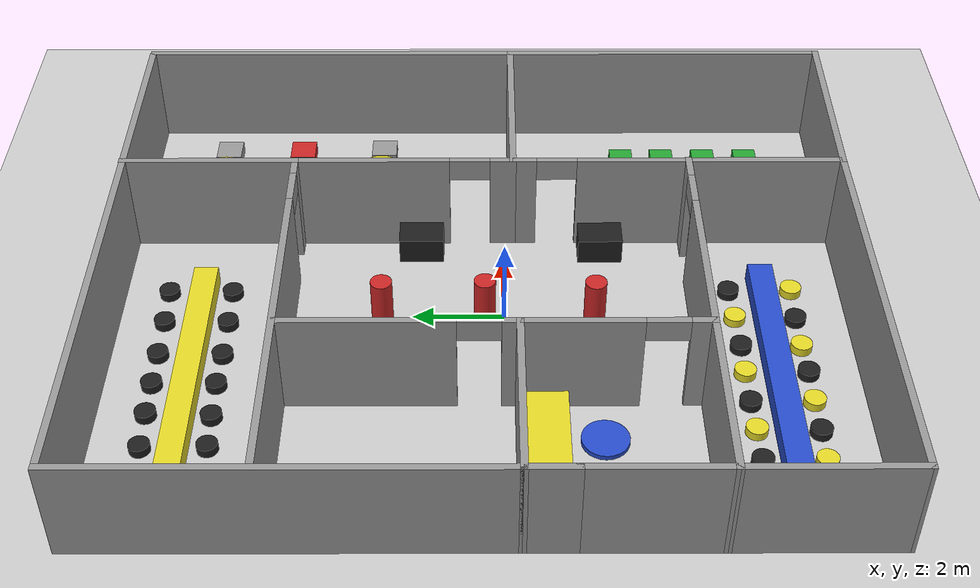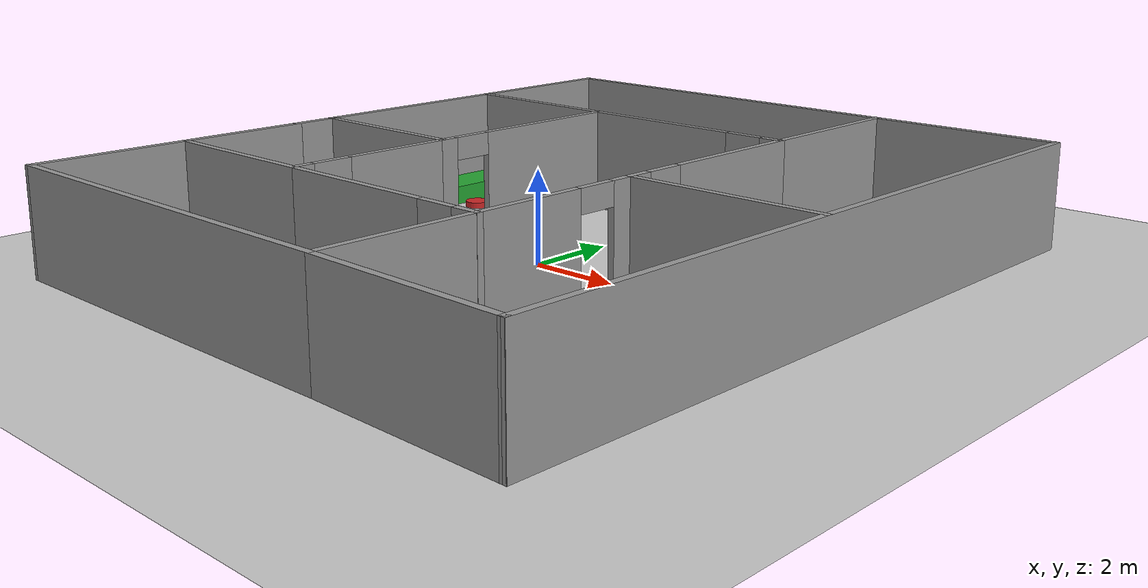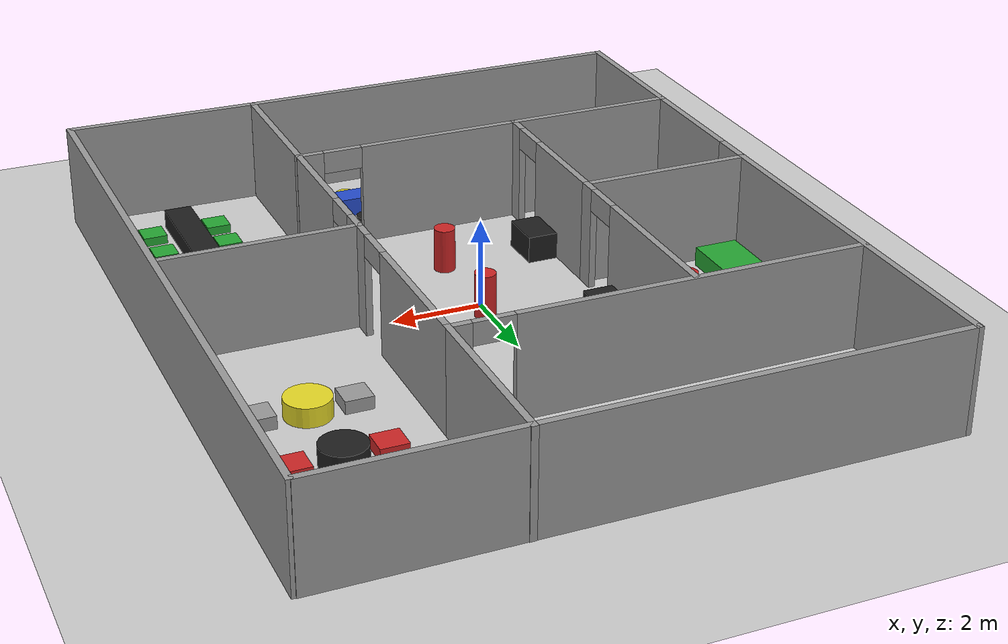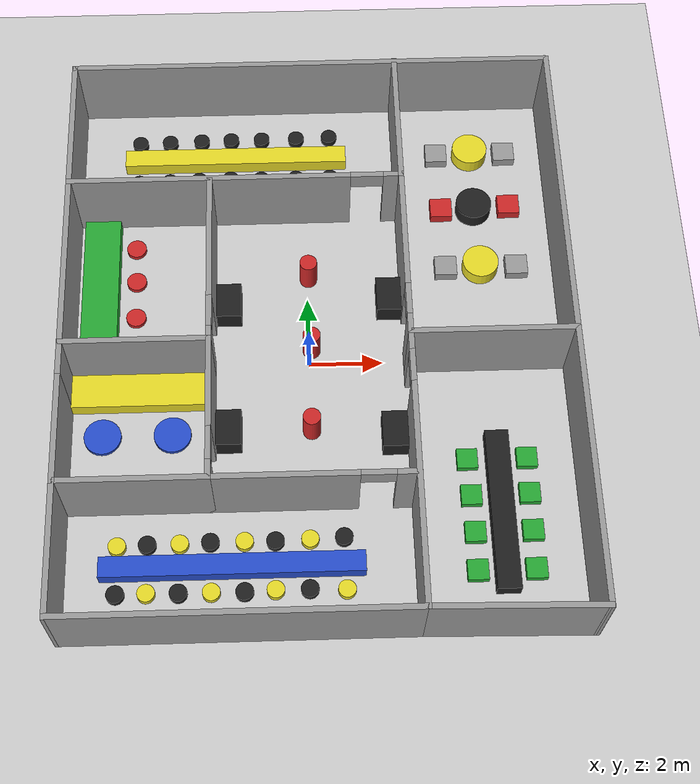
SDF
<sdf version="1.7">
 <world name="default">
  <light name="sun" type="directional">
   <pose>0 0 10 0 -0 0</pose>
   <diffuse>0.8 0.8 0.8 1</diffuse>
   <specular>0.2 0.2 0.2 1</specular>
   <attenuation>
    <range>1000</range>
    <constant>0.9</constant>
    <linear>0.01</linear>
    <quadratic>0.001</quadratic>
   </attenuation>
   <direction>-0.5 0.1 -0.9</direction>
   <spot><inner_angle>0</inner_angle><outer_angle>0</outer_angle><falloff>0</falloff></spot>
  </light>
  <model name="ground_plane">
   <static>1</static>
   <link name="link">
    <collision name="collision">
     <geometry><plane><normal>0 0 1</normal><size>100 100</size></plane></geometry>
     <surface>
      <contact><collide_bitmask>65535</collide_bitmask></contact>
      <friction><ode><mu>100</mu><mu2>50</mu2></ode></friction>
     </surface>
    </collision>
    <visual name="visual">
     <cast_shadows>0</cast_shadows>
     <geometry><plane><normal>0 0 1</normal><size>100 100</size></plane></geometry>
     <material>
      <script><uri>file://media/materials/scripts/gazebo.material</uri><name>Gazebo/Grey</name></script>
     </material>
    </visual>
   </link>
  </model>
  <gravity>0 0 -9.8</gravity>
  <magnetic_field>6e-06 2.3e-05 -4.2e-05</magnetic_field>
  <atmosphere type="adiabatic"/>
  <physics type="ode">
   <max_step_size>0.001</max_step_size>
   <real_time_factor>1</real_time_factor>
   <real_time_update_rate>1000</real_time_update_rate>
  </physics>
  <scene><ambient>0.4 0.4 0.4 1</ambient><background>0.7 0.7 0.7 1</background><shadows>1</shadows></scene>
  <spherical_coordinates>
   <surface_model>EARTH_WGS84</surface_model>
   <latitude_deg>0</latitude_deg>
   <longitude_deg>0</longitude_deg>
   <elevation>0</elevation>
   <heading_deg>0</heading_deg>
  </spherical_coordinates>
  <model name="my_room">
   <link name="link_0">
    <inertial>
     <mass>0.22579</mass>
     <inertia>
      <ixx>0.0220021</ixx>
      <ixy>0</ixy>
      <ixz>0</ixz>
      <iyy>0.0220021</iyy>
      <iyz>0</iyz>
      <izz>0.00637244</izz>
     </inertia>
    </inertial>
    <pose>0.036507 0.144422 0.125 0 -0 0</pose>
    <visual name="visual">
     <geometry><cylinder><radius>0.237583</radius><length>1</length></cylinder></geometry>
     <material>
      <lighting>1</lighting>
      <script><uri>file://media/materials/scripts/gazebo.material</uri><name>Gazebo/Red</name></script>
      <shader type="pixel"><normal_map>__default__</normal_map></shader>
      <ambient>1 0 0 1</ambient>
      <diffuse>1 0 0 1</diffuse>
      <specular>0.1 0.1 0.1 1</specular>
      <emissive>0 0 0 1</emissive>
     </material>
    </visual>
    <collision name="collision">
     <geometry><cylinder><radius>0.237583</radius><length>1</length></cylinder></geometry>
     <surface>
      <friction>
       <ode><mu>1</mu><mu2>1</mu2><fdir1>0 0 0</fdir1><slip1>0</slip1><slip2>0</slip2></ode>
       <torsional>
        <coefficient>1</coefficient>
        <patch_radius>0</patch_radius>
        <surface_radius>0</surface_radius>
        <use_patch_radius>1</use_patch_radius>
        <ode><slip>0</slip></ode>
       </torsional>
      </friction>
      <bounce><restitution_coefficient>0</restitution_coefficient><threshold>1e+06</threshold></bounce>
      <contact>
       <collide_without_contact>0</collide_without_contact>
       <collide_without_contact_bitmask>1</collide_without_contact_bitmask>
       <collide_bitmask>1</collide_bitmask>
       <ode>
        <soft_cfm>0</soft_cfm>
        <soft_erp>0.2</soft_erp>
        <kp>1e+13</kp>
        <kd>1</kd>
        <max_vel>0.01</max_vel>
        <min_depth>0</min_depth>
       </ode>
       <bullet>
        <split_impulse>1</split_impulse>
        <split_impulse_penetration_threshold>-0.01</split_impulse_penetration_threshold>
        <soft_cfm>0</soft_cfm>
        <soft_erp>0.2</soft_erp>
        <kp>1e+13</kp>
        <kd>1</kd>
       </bullet>
      </contact>
     </surface>
    </collision>
   </link>
   <link name="link_0_clone">
    <inertial>
     <mass>0.22579</mass>
     <inertia>
      <ixx>0.0220021</ixx>
      <ixy>0</ixy>
      <ixz>0</ixz>
      <iyy>0.0220021</iyy>
      <iyz>0</iyz>
      <izz>0.00637244</izz>
     </inertia>
    </inertial>
    <pose>0.006121 2.38529 0.125 0 -0 0</pose>
    <visual name="visual">
     <geometry><cylinder><radius>0.237583</radius><length>1</length></cylinder></geometry>
     <material>
      <lighting>1</lighting>
      <script><uri>file://media/materials/scripts/gazebo.material</uri><name>Gazebo/Red</name></script>
      <shader type="pixel"><normal_map>__default__</normal_map></shader>
      <ambient>1 0 0 1</ambient>
      <diffuse>1 0 0 1</diffuse>
      <specular>0.1 0.1 0.1 1</specular>
      <emissive>0 0 0 1</emissive>
     </material>
    </visual>
    <collision name="collision">
     <geometry><cylinder><radius>0.237583</radius><length>1</length></cylinder></geometry>
     <surface>
      <friction>
       <ode><mu>1</mu><mu2>1</mu2><fdir1>0 0 0</fdir1><slip1>0</slip1><slip2>0</slip2></ode>
       <torsional>
        <coefficient>1</coefficient>
        <patch_radius>0</patch_radius>
        <surface_radius>0</surface_radius>
        <use_patch_radius>1</use_patch_radius>
        <ode><slip>0</slip></ode>
       </torsional>
      </friction>
      <bounce><restitution_coefficient>0</restitution_coefficient><threshold>1e+06</threshold></bounce>
      <contact>
       <collide_without_contact>0</collide_without_contact>
       <collide_without_contact_bitmask>1</collide_without_contact_bitmask>
       <collide_bitmask>1</collide_bitmask>
       <ode>
        <soft_cfm>0</soft_cfm>
        <soft_erp>0.2</soft_erp>
        <kp>1e+13</kp>
        <kd>1</kd>
        <max_vel>0.01</max_vel>
        <min_depth>0</min_depth>
       </ode>
       <bullet>
        <split_impulse>1</split_impulse>
        <split_impulse_penetration_threshold>-0.01</split_impulse_penetration_threshold>
        <soft_cfm>0</soft_cfm>
        <soft_erp>0.2</soft_erp>
        <kp>1e+13</kp>
        <kd>1</kd>
       </bullet>
      </contact>
     </surface>
    </collision>
   </link>
   <link name="link_0_clone_0">
    <inertial>
     <mass>0.22579</mass>
     <inertia>
      <ixx>0.0220021</ixx>
      <ixy>0</ixy>
      <ixz>0</ixz>
      <iyy>0.0220021</iyy>
      <iyz>0</iyz>
      <izz>0.00637244</izz>
     </inertia>
    </inertial>
    <pose>-0.012744 -2.25733 0.125 0 -0 0</pose>
    <visual name="visual">
     <geometry><cylinder><radius>0.237583</radius><length>1</length></cylinder></geometry>
     <material>
      <lighting>1</lighting>
      <script><uri>file://media/materials/scripts/gazebo.material</uri><name>Gazebo/Red</name></script>
      <shader type="pixel"><normal_map>__default__</normal_map></shader>
      <ambient>1 0 0 1</ambient>
      <diffuse>1 0 0 1</diffuse>
      <specular>0.1 0.1 0.1 1</specular>
      <emissive>0 0 0 1</emissive>
     </material>
    </visual>
    <collision name="collision">
     <geometry><cylinder><radius>0.237583</radius><length>1</length></cylinder></geometry>
     <surface>
      <friction>
       <ode><mu>1</mu><mu2>1</mu2><fdir1>0 0 0</fdir1><slip1>0</slip1><slip2>0</slip2></ode>
       <torsional>
        <coefficient>1</coefficient>
        <patch_radius>0</patch_radius>
        <surface_radius>0</surface_radius>
        <use_patch_radius>1</use_patch_radius>
        <ode><slip>0</slip></ode>
       </torsional>
      </friction>
      <bounce><restitution_coefficient>0</restitution_coefficient><threshold>1e+06</threshold></bounce>
      <contact>
       <collide_without_contact>0</collide_without_contact>
       <collide_without_contact_bitmask>1</collide_without_contact_bitmask>
       <collide_bitmask>1</collide_bitmask>
       <ode>
        <soft_cfm>0</soft_cfm>
        <soft_erp>0.2</soft_erp>
        <kp>1e+13</kp>
        <kd>1</kd>
        <max_vel>0.01</max_vel>
        <min_depth>0</min_depth>
       </ode>
       <bullet>
        <split_impulse>1</split_impulse>
        <split_impulse_penetration_threshold>-0.01</split_impulse_penetration_threshold>
        <soft_cfm>0</soft_cfm>
        <soft_erp>0.2</soft_erp>
        <kp>1e+13</kp>
        <kd>1</kd>
       </bullet>
      </contact>
     </surface>
    </collision>
   </link>
   <model name="room_main">
    <link name="link_0">
     <inertial>
      <mass>0.681238</mass>
      <inertia>
       <ixx>0.11354</ixx>
       <ixy>0</ixy>
       <ixz>0</ixz>
       <iyy>0.0831162</iyy>
       <iyz>0</iyz>
       <izz>0.0831162</izz>
      </inertia>
     </inertial>
     <pose>-2.17187 1.76358 0.089596 0 -0 0</pose>
     <visual name="visual">
      <geometry><box><size>0.681243 1 1</size></box></geometry>
      <material>
       <lighting>1</lighting>
       <script><uri>file://media/materials/scripts/gazebo.material</uri><name>Gazebo/Black</name></script>
       <shader type="pixel"><normal_map>__default__</normal_map></shader>
       <ambient>0 0 0 1</ambient>
       <diffuse>0 0 0 1</diffuse>
       <specular>0.1 0.1 0.1 1</specular>
       <emissive>0 0 0 1</emissive>
      </material>
     </visual>
     <collision name="collision">
      <geometry><box><size>0.681243 1 1</size></box></geometry>
      <surface>
       <friction>
        <ode><mu>1</mu><mu2>1</mu2><fdir1>0 0 0</fdir1><slip1>0</slip1><slip2>0</slip2></ode>
        <torsional>
         <coefficient>1</coefficient>
         <patch_radius>0</patch_radius>
         <surface_radius>0</surface_radius>
         <use_patch_radius>1</use_patch_radius>
         <ode><slip>0</slip></ode>
        </torsional>
       </friction>
       <bounce><restitution_coefficient>0</restitution_coefficient><threshold>1e+06</threshold></bounce>
       <contact>
        <collide_without_contact>0</collide_without_contact>
        <collide_without_contact_bitmask>1</collide_without_contact_bitmask>
        <collide_bitmask>1</collide_bitmask>
        <ode>
         <soft_cfm>0</soft_cfm>
         <soft_erp>0.2</soft_erp>
         <kp>1e+13</kp>
         <kd>1</kd>
         <max_vel>0.01</max_vel>
         <min_depth>0</min_depth>
        </ode>
        <bullet>
         <split_impulse>1</split_impulse>
         <split_impulse_penetration_threshold>-0.01</split_impulse_penetration_threshold>
         <soft_cfm>0</soft_cfm>
         <soft_erp>0.2</soft_erp>
         <kp>1e+13</kp>
         <kd>1</kd>
        </bullet>
       </contact>
      </surface>
     </collision>
    </link>
    <link name="link_0_clone">
     <inertial>
      <mass>0.681238</mass>
      <inertia>
       <ixx>0.11354</ixx>
       <ixy>0</ixy>
       <ixz>0</ixz>
       <iyy>0.0831162</iyy>
       <iyz>0</iyz>
       <izz>0.0831162</izz>
      </inertia>
     </inertial>
     <pose>2.22803 1.85215 0.089596 0 -0 0</pose>
     <visual name="visual">
      <geometry><box><size>0.681243 1 1</size></box></geometry>
      <material>
       <lighting>1</lighting>
       <script><uri>file://media/materials/scripts/gazebo.material</uri><name>Gazebo/Black</name></script>
       <shader type="pixel"><normal_map>__default__</normal_map></shader>
       <ambient>0 0 0 1</ambient>
       <diffuse>0 0 0 1</diffuse>
       <specular>0.1 0.1 0.1 1</specular>
       <emissive>0 0 0 1</emissive>
      </material>
     </visual>
     <collision name="collision">
      <geometry><box><size>0.681243 1 1</size></box></geometry>
      <surface>
       <friction>
        <ode><mu>1</mu><mu2>1</mu2><fdir1>0 0 0</fdir1><slip1>0</slip1><slip2>0</slip2></ode>
        <torsional>
         <coefficient>1</coefficient>
         <patch_radius>0</patch_radius>
         <surface_radius>0</surface_radius>
         <use_patch_radius>1</use_patch_radius>
         <ode><slip>0</slip></ode>
        </torsional>
       </friction>
       <bounce><restitution_coefficient>0</restitution_coefficient><threshold>1e+06</threshold></bounce>
       <contact>
        <collide_without_contact>0</collide_without_contact>
        <collide_without_contact_bitmask>1</collide_without_contact_bitmask>
        <collide_bitmask>1</collide_bitmask>
        <ode>
         <soft_cfm>0</soft_cfm>
         <soft_erp>0.2</soft_erp>
         <kp>1e+13</kp>
         <kd>1</kd>
         <max_vel>0.01</max_vel>
         <min_depth>0</min_depth>
        </ode>
        <bullet>
         <split_impulse>1</split_impulse>
         <split_impulse_penetration_threshold>-0.01</split_impulse_penetration_threshold>
         <soft_cfm>0</soft_cfm>
         <soft_erp>0.2</soft_erp>
         <kp>1e+13</kp>
         <kd>1</kd>
        </bullet>
       </contact>
      </surface>
     </collision>
    </link>
    <link name="link_0_clone_0">
     <inertial>
      <mass>0.681238</mass>
      <inertia>
       <ixx>0.11354</ixx>
       <ixy>0</ixy>
       <ixz>0</ixz>
       <iyy>0.0831162</iyy>
       <iyz>0</iyz>
       <izz>0.0831162</izz>
      </inertia>
     </inertial>
     <pose>2.2069 -2.20031 0.089596 0 -0 0</pose>
     <visual name="visual">
      <geometry><box><size>0.681243 1 1</size></box></geometry>
      <material>
       <lighting>1</lighting>
       <script><uri>file://media/materials/scripts/gazebo.material</uri><name>Gazebo/Black</name></script>
       <shader type="pixel"><normal_map>__default__</normal_map></shader>
       <ambient>0 0 0 1</ambient>
       <diffuse>0 0 0 1</diffuse>
       <specular>0.1 0.1 0.1 1</specular>
       <emissive>0 0 0 1</emissive>
      </material>
     </visual>
     <collision name="collision">
      <geometry><box><size>0.681243 1 1</size></box></geometry>
      <surface>
       <friction>
        <ode><mu>1</mu><mu2>1</mu2><fdir1>0 0 0</fdir1><slip1>0</slip1><slip2>0</slip2></ode>
        <torsional>
         <coefficient>1</coefficient>
         <patch_radius>0</patch_radius>
         <surface_radius>0</surface_radius>
         <use_patch_radius>1</use_patch_radius>
         <ode><slip>0</slip></ode>
        </torsional>
       </friction>
       <bounce><restitution_coefficient>0</restitution_coefficient><threshold>1e+06</threshold></bounce>
       <contact>
        <collide_without_contact>0</collide_without_contact>
        <collide_without_contact_bitmask>1</collide_without_contact_bitmask>
        <collide_bitmask>1</collide_bitmask>
        <ode>
         <soft_cfm>0</soft_cfm>
         <soft_erp>0.2</soft_erp>
         <kp>1e+13</kp>
         <kd>1</kd>
         <max_vel>0.01</max_vel>
         <min_depth>0</min_depth>
        </ode>
        <bullet>
         <split_impulse>1</split_impulse>
         <split_impulse_penetration_threshold>-0.01</split_impulse_penetration_threshold>
         <soft_cfm>0</soft_cfm>
         <soft_erp>0.2</soft_erp>
         <kp>1e+13</kp>
         <kd>1</kd>
        </bullet>
       </contact>
      </surface>
     </collision>
    </link>
    <link name="link_0_clone_1">
     <inertial>
      <mass>0.681238</mass>
      <inertia>
       <ixx>0.11354</ixx>
       <ixy>0</ixy>
       <ixz>0</ixz>
       <iyy>0.0831162</iyy>
       <iyz>0</iyz>
       <izz>0.0831162</izz>
      </inertia>
     </inertial>
     <pose>-2.18714 -2.04539 0.089596 0 -0 0</pose>
     <visual name="visual">
      <geometry><box><size>0.681243 1 1</size></box></geometry>
      <material>
       <lighting>1</lighting>
       <script><uri>file://media/materials/scripts/gazebo.material</uri><name>Gazebo/Black</name></script>
       <shader type="pixel"><normal_map>__default__</normal_map></shader>
       <ambient>0 0 0 1</ambient>
       <diffuse>0 0 0 1</diffuse>
       <specular>0.1 0.1 0.1 1</specular>
       <emissive>0 0 0 1</emissive>
      </material>
     </visual>
     <collision name="collision">
      <geometry><box><size>0.681243 1 1</size></box></geometry>
      <surface>
       <friction>
        <ode><mu>1</mu><mu2>1</mu2><fdir1>0 0 0</fdir1><slip1>0</slip1><slip2>0</slip2></ode>
        <torsional>
         <coefficient>1</coefficient>
         <patch_radius>0</patch_radius>
         <surface_radius>0</surface_radius>
         <use_patch_radius>1</use_patch_radius>
         <ode><slip>0</slip></ode>
        </torsional>
       </friction>
       <bounce><restitution_coefficient>0</restitution_coefficient><threshold>1e+06</threshold></bounce>
       <contact>
        <collide_without_contact>0</collide_without_contact>
        <collide_without_contact_bitmask>1</collide_without_contact_bitmask>
        <collide_bitmask>1</collide_bitmask>
        <ode>
         <soft_cfm>0</soft_cfm>
         <soft_erp>0.2</soft_erp>
         <kp>1e+13</kp>
         <kd>1</kd>
         <max_vel>0.01</max_vel>
         <min_depth>0</min_depth>
        </ode>
        <bullet>
         <split_impulse>1</split_impulse>
         <split_impulse_penetration_threshold>-0.01</split_impulse_penetration_threshold>
         <soft_cfm>0</soft_cfm>
         <soft_erp>0.2</soft_erp>
         <kp>1e+13</kp>
         <kd>1</kd>
        </bullet>
       </contact>
      </surface>
     </collision>
    </link>
    <model name="New_meeting">
     <link name="link_0">
      <inertial>
       <mass>3.73645</mass>
       <inertia><ixx>0.622742</ixx><ixy>0</ixy><ixz>0</ixz><iyy>4.65838</iyy><iyz>0</iyz><izz>4.65838</izz></inertia>
      </inertial>
      <pose>-4.22564 -0.997257 0.089815 0 -0 0</pose>
      <visual name="visual">
       <geometry><box><size>3.73642 1 1</size></box></geometry>
       <material>
        <lighting>1</lighting>
        <script><uri>file://media/materials/scripts/gazebo.material</uri><name>Gazebo/Yellow</name></script>
        <shader type="pixel"><normal_map>__default__</normal_map></shader>
        <ambient>1 1 0 1</ambient>
        <diffuse>1 1 0 1</diffuse>
        <emissive>0 0 0 1</emissive>
       </material>
      </visual>
      <collision name="collision">
       <geometry><box><size>3.73642 1 1</size></box></geometry>
       <surface>
        <friction>
         <ode><mu>1</mu><mu2>1</mu2><fdir1>0 0 0</fdir1><slip1>0</slip1><slip2>0</slip2></ode>
         <torsional>
          <coefficient>1</coefficient>
          <patch_radius>0</patch_radius>
          <surface_radius>0</surface_radius>
          <use_patch_radius>1</use_patch_radius>
          <ode><slip>0</slip></ode>
         </torsional>
        </friction>
        <bounce><restitution_coefficient>0</restitution_coefficient><threshold>1e+06</threshold></bounce>
        <contact>
         <collide_without_contact>0</collide_without_contact>
         <collide_without_contact_bitmask>1</collide_without_contact_bitmask>
         <collide_bitmask>1</collide_bitmask>
         <ode>
          <soft_cfm>0</soft_cfm>
          <soft_erp>0.2</soft_erp>
          <kp>1e+13</kp>
          <kd>1</kd>
          <max_vel>0.01</max_vel>
          <min_depth>0</min_depth>
         </ode>
         <bullet>
          <split_impulse>1</split_impulse>
          <split_impulse_penetration_threshold>-0.01</split_impulse_penetration_threshold>
          <soft_cfm>0</soft_cfm>
          <soft_erp>0.2</soft_erp>
          <kp>1e+13</kp>
          <kd>1</kd>
         </bullet>
        </contact>
       </surface>
      </collision>
     </link>
     <link name="link_1">
      <inertial>
       <mass>0.660923</mass>
       <inertia>
        <ixx>0.0653661</ixx>
        <ixy>0</ixy>
        <ixz>0</ixz>
        <iyy>0.0653661</iyy>
        <iyz>0</iyz>
        <izz>0.0826154</izz>
       </inertia>
      </inertial>
      <pose>-5.2249 -2.22761 -0.064595 0 -0 0</pose>
      <visual name="visual">
       <geometry><cylinder><radius>0.5</radius><length>0.66092</length></cylinder></geometry>
       <material>
        <lighting>1</lighting>
        <script><uri>file://media/materials/scripts/gazebo.material</uri><name>Gazebo/Blue</name></script>
        <shader type="pixel"><normal_map>__default__</normal_map></shader>
        <ambient>0 0 1 1</ambient>
        <diffuse>0 0 1 1</diffuse>
        <specular>0.1 0.1 0.1 1</specular>
        <emissive>0 0 0 1</emissive>
       </material>
      </visual>
      <collision name="collision">
       <geometry><cylinder><radius>0.5</radius><length>0.66092</length></cylinder></geometry>
       <surface>
        <friction>
         <ode><mu>1</mu><mu2>1</mu2><fdir1>0 0 0</fdir1><slip1>0</slip1><slip2>0</slip2></ode>
         <torsional>
          <coefficient>1</coefficient>
          <patch_radius>0</patch_radius>
          <surface_radius>0</surface_radius>
          <use_patch_radius>1</use_patch_radius>
          <ode><slip>0</slip></ode>
         </torsional>
        </friction>
        <bounce><restitution_coefficient>0</restitution_coefficient><threshold>1e+06</threshold></bounce>
        <contact>
         <collide_without_contact>0</collide_without_contact>
         <collide_without_contact_bitmask>1</collide_without_contact_bitmask>
         <collide_bitmask>1</collide_bitmask>
         <ode>
          <soft_cfm>0</soft_cfm>
          <soft_erp>0.2</soft_erp>
          <kp>1e+13</kp>
          <kd>1</kd>
          <max_vel>0.01</max_vel>
          <min_depth>0</min_depth>
         </ode>
         <bullet>
          <split_impulse>1</split_impulse>
          <split_impulse_penetration_threshold>-0.01</split_impulse_penetration_threshold>
          <soft_cfm>0</soft_cfm>
          <soft_erp>0.2</soft_erp>
          <kp>1e+13</kp>
          <kd>1</kd>
         </bullet>
        </contact>
       </surface>
      </collision>
     </link>
     <link name="link_10">
      <inertial>
       <mass>2.70448</mass>
       <inertia><ixx>4.45333</ixx><ixy>0</ixy><ixz>0</ixz><iyy>0.313243</iyy><iyz>0</iyz><izz>4.31583</izz></inertia>
      </inertial>
      <pose>5.21193 -4.62527 0.089815 0 -0 0</pose>
      <visual name="visual">
       <geometry><box><size>0.624406 4.33126 1</size></box></geometry>
       <material>
        <lighting>1</lighting>
        <script><uri>file://media/materials/scripts/gazebo.material</uri><name>Gazebo/Black</name></script>
        <shader type="pixel"><normal_map>__default__</normal_map></shader>
        <ambient>0 0 0 1</ambient>
        <diffuse>0 0 0 1</diffuse>
        <specular>0.1 0.1 0.1 1</specular>
        <emissive>0 0 0 1</emissive>
       </material>
      </visual>
      <collision name="collision">
       <geometry><box><size>0.624406 4.33126 1</size></box></geometry>
       <surface>
        <friction>
         <ode><mu>1</mu><mu2>1</mu2><fdir1>0 0 0</fdir1><slip1>0</slip1><slip2>0</slip2></ode>
         <torsional>
          <coefficient>1</coefficient>
          <patch_radius>0</patch_radius>
          <surface_radius>0</surface_radius>
          <use_patch_radius>1</use_patch_radius>
          <ode><slip>0</slip></ode>
         </torsional>
        </friction>
        <bounce><restitution_coefficient>0</restitution_coefficient><threshold>1e+06</threshold></bounce>
        <contact>
         <collide_without_contact>0</collide_without_contact>
         <collide_without_contact_bitmask>1</collide_without_contact_bitmask>
         <collide_bitmask>1</collide_bitmask>
         <ode>
          <soft_cfm>0</soft_cfm>
          <soft_erp>0.2</soft_erp>
          <kp>1e+13</kp>
          <kd>1</kd>
          <max_vel>0.01</max_vel>
          <min_depth>0</min_depth>
         </ode>
         <bullet>
          <split_impulse>1</split_impulse>
          <split_impulse_penetration_threshold>-0.01</split_impulse_penetration_threshold>
          <soft_cfm>0</soft_cfm>
          <soft_erp>0.2</soft_erp>
          <kp>1e+13</kp>
          <kd>1</kd>
         </bullet>
        </contact>
       </surface>
      </collision>
     </link>
     <link name="link_11">
      <inertial>
       <mass>0.220061</mass>
       <inertia>
        <ixx>0.0155168</ixx>
        <ixy>0</ixy>
        <ixz>0</ixz>
        <iyy>0.015534</iyy>
        <iyz>0</iyz>
        <izz>0.0108839</izz>
       </inertia>
      </inertial>
      <pose>4.47508 -6.19658 -0.011082 0 -0 0</pose>
      <visual name="visual">
       <geometry><box><size>0.545179 0.54432 0.741521</size></box></geometry>
       <material>
        <lighting>1</lighting>
        <script><uri>file://media/materials/scripts/gazebo.material</uri><name>Gazebo/Green</name></script>
        <shader type="pixel"><normal_map>__default__</normal_map></shader>
        <ambient>0 1 0 1</ambient>
        <diffuse>0 1 0 1</diffuse>
        <specular>0.1 0.1 0.1 1</specular>
        <emissive>0 0 0 1</emissive>
       </material>
      </visual>
      <collision name="collision">
       <geometry><box><size>0.545179 0.54432 0.741521</size></box></geometry>
       <surface>
        <friction>
         <ode><mu>1</mu><mu2>1</mu2><fdir1>0 0 0</fdir1><slip1>0</slip1><slip2>0</slip2></ode>
         <torsional>
          <coefficient>1</coefficient>
          <patch_radius>0</patch_radius>
          <surface_radius>0</surface_radius>
          <use_patch_radius>1</use_patch_radius>
          <ode><slip>0</slip></ode>
         </torsional>
        </friction>
        <bounce><restitution_coefficient>0</restitution_coefficient><threshold>1e+06</threshold></bounce>
        <contact>
         <collide_without_contact>0</collide_without_contact>
         <collide_without_contact_bitmask>1</collide_without_contact_bitmask>
         <collide_bitmask>1</collide_bitmask>
         <ode>
          <soft_cfm>0</soft_cfm>
          <soft_erp>0.2</soft_erp>
          <kp>1e+13</kp>
          <kd>1</kd>
          <max_vel>0.01</max_vel>
          <min_depth>0</min_depth>
         </ode>
         <bullet>
          <split_impulse>1</split_impulse>
          <split_impulse_penetration_threshold>-0.01</split_impulse_penetration_threshold>
          <soft_cfm>0</soft_cfm>
          <soft_erp>0.2</soft_erp>
          <kp>1e+13</kp>
          <kd>1</kd>
         </bullet>
        </contact>
       </surface>
      </collision>
     </link>
     <link name="link_11_clone">
      <inertial>
       <mass>0.220061</mass>
       <inertia>
        <ixx>0.0155168</ixx>
        <ixy>0</ixy>
        <ixz>0</ixz>
        <iyy>0.015534</iyy>
        <iyz>0</iyz>
        <izz>0.0108839</izz>
       </inertia>
      </inertial>
      <pose>4.48557 -5.17564 -0.011082 0 -0 0</pose>
      <visual name="visual">
       <geometry><box><size>0.545179 0.54432 0.741521</size></box></geometry>
       <material>
        <lighting>1</lighting>
        <script><uri>file://media/materials/scripts/gazebo.material</uri><name>Gazebo/Green</name></script>
        <shader type="pixel"><normal_map>__default__</normal_map></shader>
        <ambient>0 1 0 1</ambient>
        <diffuse>0 1 0 1</diffuse>
        <specular>0.1 0.1 0.1 1</specular>
        <emissive>0 0 0 1</emissive>
       </material>
      </visual>
      <collision name="collision">
       <geometry><box><size>0.545179 0.54432 0.741521</size></box></geometry>
       <surface>
        <friction>
         <ode><mu>1</mu><mu2>1</mu2><fdir1>0 0 0</fdir1><slip1>0</slip1><slip2>0</slip2></ode>
         <torsional>
          <coefficient>1</coefficient>
          <patch_radius>0</patch_radius>
          <surface_radius>0</surface_radius>
          <use_patch_radius>1</use_patch_radius>
          <ode><slip>0</slip></ode>
         </torsional>
        </friction>
        <bounce><restitution_coefficient>0</restitution_coefficient><threshold>1e+06</threshold></bounce>
        <contact>
         <collide_without_contact>0</collide_without_contact>
         <collide_without_contact_bitmask>1</collide_without_contact_bitmask>
         <collide_bitmask>1</collide_bitmask>
         <ode>
          <soft_cfm>0</soft_cfm>
          <soft_erp>0.2</soft_erp>
          <kp>1e+13</kp>
          <kd>1</kd>
          <max_vel>0.01</max_vel>
          <min_depth>0</min_depth>
         </ode>
         <bullet>
          <split_impulse>1</split_impulse>
          <split_impulse_penetration_threshold>-0.01</split_impulse_penetration_threshold>
          <soft_cfm>0</soft_cfm>
          <soft_erp>0.2</soft_erp>
          <kp>1e+13</kp>
          <kd>1</kd>
         </bullet>
        </contact>
       </surface>
      </collision>
     </link>
     <link name="link_11_clone_0">
      <inertial>
       <mass>0.220061</mass>
       <inertia>
        <ixx>0.0155168</ixx>
        <ixy>0</ixy>
        <ixz>0</ixz>
        <iyy>0.015534</iyy>
        <iyz>0</iyz>
        <izz>0.0108839</izz>
       </inertia>
      </inertial>
      <pose>4.45475 -4.16511 -0.011082 0 -0 0</pose>
      <visual name="visual">
       <geometry><box><size>0.545179 0.54432 0.741521</size></box></geometry>
       <material>
        <lighting>1</lighting>
        <script><uri>file://media/materials/scripts/gazebo.material</uri><name>Gazebo/Green</name></script>
        <shader type="pixel"><normal_map>__default__</normal_map></shader>
        <ambient>0 1 0 1</ambient>
        <diffuse>0 1 0 1</diffuse>
        <specular>0.1 0.1 0.1 1</specular>
        <emissive>0 0 0 1</emissive>
       </material>
      </visual>
      <collision name="collision">
       <geometry><box><size>0.545179 0.54432 0.741521</size></box></geometry>
       <surface>
        <friction>
         <ode><mu>1</mu><mu2>1</mu2><fdir1>0 0 0</fdir1><slip1>0</slip1><slip2>0</slip2></ode>
         <torsional>
          <coefficient>1</coefficient>
          <patch_radius>0</patch_radius>
          <surface_radius>0</surface_radius>
          <use_patch_radius>1</use_patch_radius>
          <ode><slip>0</slip></ode>
         </torsional>
        </friction>
        <bounce><restitution_coefficient>0</restitution_coefficient><threshold>1e+06</threshold></bounce>
        <contact>
         <collide_without_contact>0</collide_without_contact>
         <collide_without_contact_bitmask>1</collide_without_contact_bitmask>
         <collide_bitmask>1</collide_bitmask>
         <ode>
          <soft_cfm>0</soft_cfm>
          <soft_erp>0.2</soft_erp>
          <kp>1e+13</kp>
          <kd>1</kd>
          <max_vel>0.01</max_vel>
          <min_depth>0</min_depth>
         </ode>
         <bullet>
          <split_impulse>1</split_impulse>
          <split_impulse_penetration_threshold>-0.01</split_impulse_penetration_threshold>
          <soft_cfm>0</soft_cfm>
          <soft_erp>0.2</soft_erp>
          <kp>1e+13</kp>
          <kd>1</kd>
         </bullet>
        </contact>
       </surface>
      </collision>
     </link>
     <link name="link_11_clone_1">
      <inertial>
       <mass>0.220061</mass>
       <inertia>
        <ixx>0.0155168</ixx>
        <ixy>0</ixy>
        <ixz>0</ixz>
        <iyy>0.015534</iyy>
        <iyz>0</iyz>
        <izz>0.0108839</izz>
       </inertia>
      </inertial>
      <pose>4.41537 -3.14855 -0.011082 0 -0 0</pose>
      <visual name="visual">
       <geometry><box><size>0.545179 0.54432 0.741521</size></box></geometry>
       <material>
        <lighting>1</lighting>
        <script><uri>file://media/materials/scripts/gazebo.material</uri><name>Gazebo/Green</name></script>
        <shader type="pixel"><normal_map>__default__</normal_map></shader>
        <ambient>0 1 0 1</ambient>
        <diffuse>0 1 0 1</diffuse>
        <specular>0.1 0.1 0.1 1</specular>
        <emissive>0 0 0 1</emissive>
       </material>
      </visual>
      <collision name="collision">
       <geometry><box><size>0.545179 0.54432 0.741521</size></box></geometry>
       <surface>
        <friction>
         <ode><mu>1</mu><mu2>1</mu2><fdir1>0 0 0</fdir1><slip1>0</slip1><slip2>0</slip2></ode>
         <torsional>
          <coefficient>1</coefficient>
          <patch_radius>0</patch_radius>
          <surface_radius>0</surface_radius>
          <use_patch_radius>1</use_patch_radius>
          <ode><slip>0</slip></ode>
         </torsional>
        </friction>
        <bounce><restitution_coefficient>0</restitution_coefficient><threshold>1e+06</threshold></bounce>
        <contact>
         <collide_without_contact>0</collide_without_contact>
         <collide_without_contact_bitmask>1</collide_without_contact_bitmask>
         <collide_bitmask>1</collide_bitmask>
         <ode>
          <soft_cfm>0</soft_cfm>
          <soft_erp>0.2</soft_erp>
          <kp>1e+13</kp>
          <kd>1</kd>
          <max_vel>0.01</max_vel>
          <min_depth>0</min_depth>
         </ode>
         <bullet>
          <split_impulse>1</split_impulse>
          <split_impulse_penetration_threshold>-0.01</split_impulse_penetration_threshold>
          <soft_cfm>0</soft_cfm>
          <soft_erp>0.2</soft_erp>
          <kp>1e+13</kp>
          <kd>1</kd>
         </bullet>
        </contact>
       </surface>
      </collision>
     </link>
     <link name="link_11_clone_2">
      <inertial>
       <mass>0.220061</mass>
       <inertia>
        <ixx>0.0155168</ixx>
        <ixy>0</ixy>
        <ixz>0</ixz>
        <iyy>0.015534</iyy>
        <iyz>0</iyz>
        <izz>0.0108839</izz>
       </inertia>
      </inertial>
      <pose>5.99181 -3.14543 -0.011082 0 -0 0</pose>
      <visual name="visual">
       <geometry><box><size>0.545179 0.54432 0.741521</size></box></geometry>
       <material>
        <lighting>1</lighting>
        <script><uri>file://media/materials/scripts/gazebo.material</uri><name>Gazebo/Green</name></script>
        <shader type="pixel"><normal_map>__default__</normal_map></shader>
        <ambient>0 1 0 1</ambient>
        <diffuse>0 1 0 1</diffuse>
        <specular>0.1 0.1 0.1 1</specular>
        <emissive>0 0 0 1</emissive>
       </material>
      </visual>
      <collision name="collision">
       <geometry><box><size>0.545179 0.54432 0.741521</size></box></geometry>
       <surface>
        <friction>
         <ode><mu>1</mu><mu2>1</mu2><fdir1>0 0 0</fdir1><slip1>0</slip1><slip2>0</slip2></ode>
         <torsional>
          <coefficient>1</coefficient>
          <patch_radius>0</patch_radius>
          <surface_radius>0</surface_radius>
          <use_patch_radius>1</use_patch_radius>
          <ode><slip>0</slip></ode>
         </torsional>
        </friction>
        <bounce><restitution_coefficient>0</restitution_coefficient><threshold>1e+06</threshold></bounce>
        <contact>
         <collide_without_contact>0</collide_without_contact>
         <collide_without_contact_bitmask>1</collide_without_contact_bitmask>
         <collide_bitmask>1</collide_bitmask>
         <ode>
          <soft_cfm>0</soft_cfm>
          <soft_erp>0.2</soft_erp>
          <kp>1e+13</kp>
          <kd>1</kd>
          <max_vel>0.01</max_vel>
          <min_depth>0</min_depth>
         </ode>
         <bullet>
          <split_impulse>1</split_impulse>
          <split_impulse_penetration_threshold>-0.01</split_impulse_penetration_threshold>
          <soft_cfm>0</soft_cfm>
          <soft_erp>0.2</soft_erp>
          <kp>1e+13</kp>
          <kd>1</kd>
         </bullet>
        </contact>
       </surface>
      </collision>
     </link>
     <link name="link_11_clone_3">
      <inertial>
       <mass>0.220061</mass>
       <inertia>
        <ixx>0.0155168</ixx>
        <ixy>0</ixy>
        <ixz>0</ixz>
        <iyy>0.015534</iyy>
        <iyz>0</iyz>
        <izz>0.0108839</izz>
       </inertia>
      </inertial>
      <pose>5.98483 -4.13955 -0.011082 0 -0 0</pose>
      <visual name="visual">
       <geometry><box><size>0.545179 0.54432 0.741521</size></box></geometry>
       <material>
        <lighting>1</lighting>
        <script><uri>file://media/materials/scripts/gazebo.material</uri><name>Gazebo/Green</name></script>
        <shader type="pixel"><normal_map>__default__</normal_map></shader>
        <ambient>0 1 0 1</ambient>
        <diffuse>0 1 0 1</diffuse>
        <specular>0.1 0.1 0.1 1</specular>
        <emissive>0 0 0 1</emissive>
       </material>
      </visual>
      <collision name="collision">
       <geometry><box><size>0.545179 0.54432 0.741521</size></box></geometry>
       <surface>
        <friction>
         <ode><mu>1</mu><mu2>1</mu2><fdir1>0 0 0</fdir1><slip1>0</slip1><slip2>0</slip2></ode>
         <torsional>
          <coefficient>1</coefficient>
          <patch_radius>0</patch_radius>
          <surface_radius>0</surface_radius>
          <use_patch_radius>1</use_patch_radius>
          <ode><slip>0</slip></ode>
         </torsional>
        </friction>
        <bounce><restitution_coefficient>0</restitution_coefficient><threshold>1e+06</threshold></bounce>
        <contact>
         <collide_without_contact>0</collide_without_contact>
         <collide_without_contact_bitmask>1</collide_without_contact_bitmask>
         <collide_bitmask>1</collide_bitmask>
         <ode>
          <soft_cfm>0</soft_cfm>
          <soft_erp>0.2</soft_erp>
          <kp>1e+13</kp>
          <kd>1</kd>
          <max_vel>0.01</max_vel>
          <min_depth>0</min_depth>
         </ode>
         <bullet>
          <split_impulse>1</split_impulse>
          <split_impulse_penetration_threshold>-0.01</split_impulse_penetration_threshold>
          <soft_cfm>0</soft_cfm>
          <soft_erp>0.2</soft_erp>
          <kp>1e+13</kp>
          <kd>1</kd>
         </bullet>
        </contact>
       </surface>
      </collision>
     </link>
     <link name="link_11_clone_4">
      <inertial>
       <mass>0.220061</mass>
       <inertia>
        <ixx>0.0155168</ixx>
        <ixy>0</ixy>
        <ixz>0</ixz>
        <iyy>0.015534</iyy>
        <iyz>0</iyz>
        <izz>0.0108839</izz>
       </inertia>
      </inertial>
      <pose>5.97996 -5.15982 -0.011082 0 -0 0</pose>
      <visual name="visual">
       <geometry><box><size>0.545179 0.54432 0.741521</size></box></geometry>
       <material>
        <lighting>1</lighting>
        <script><uri>file://media/materials/scripts/gazebo.material</uri><name>Gazebo/Green</name></script>
        <shader type="pixel"><normal_map>__default__</normal_map></shader>
        <ambient>0 1 0 1</ambient>
        <diffuse>0 1 0 1</diffuse>
        <specular>0.1 0.1 0.1 1</specular>
        <emissive>0 0 0 1</emissive>
       </material>
      </visual>
      <collision name="collision">
       <geometry><box><size>0.545179 0.54432 0.741521</size></box></geometry>
       <surface>
        <friction>
         <ode><mu>1</mu><mu2>1</mu2><fdir1>0 0 0</fdir1><slip1>0</slip1><slip2>0</slip2></ode>
         <torsional>
          <coefficient>1</coefficient>
          <patch_radius>0</patch_radius>
          <surface_radius>0</surface_radius>
          <use_patch_radius>1</use_patch_radius>
          <ode><slip>0</slip></ode>
         </torsional>
        </friction>
        <bounce><restitution_coefficient>0</restitution_coefficient><threshold>1e+06</threshold></bounce>
        <contact>
         <collide_without_contact>0</collide_without_contact>
         <collide_without_contact_bitmask>1</collide_without_contact_bitmask>
         <collide_bitmask>1</collide_bitmask>
         <ode>
          <soft_cfm>0</soft_cfm>
          <soft_erp>0.2</soft_erp>
          <kp>1e+13</kp>
          <kd>1</kd>
          <max_vel>0.01</max_vel>
          <min_depth>0</min_depth>
         </ode>
         <bullet>
          <split_impulse>1</split_impulse>
          <split_impulse_penetration_threshold>-0.01</split_impulse_penetration_threshold>
          <soft_cfm>0</soft_cfm>
          <soft_erp>0.2</soft_erp>
          <kp>1e+13</kp>
          <kd>1</kd>
         </bullet>
        </contact>
       </surface>
      </collision>
     </link>
     <link name="link_11_clone_5">
      <inertial>
       <mass>0.220061</mass>
       <inertia>
        <ixx>0.0155168</ixx>
        <ixy>0</ixy>
        <ixz>0</ixz>
        <iyy>0.015534</iyy>
        <iyz>0</iyz>
        <izz>0.0108839</izz>
       </inertia>
      </inertial>
      <pose>5.9741 -6.19116 -0.011082 0 -0 0</pose>
      <visual name="visual">
       <geometry><box><size>0.545179 0.54432 0.741521</size></box></geometry>
       <material>
        <lighting>1</lighting>
        <script><uri>file://media/materials/scripts/gazebo.material</uri><name>Gazebo/Green</name></script>
        <shader type="pixel"><normal_map>__default__</normal_map></shader>
        <ambient>0 1 0 1</ambient>
        <diffuse>0 1 0 1</diffuse>
        <specular>0.1 0.1 0.1 1</specular>
        <emissive>0 0 0 1</emissive>
       </material>
      </visual>
      <collision name="collision">
       <geometry><box><size>0.545179 0.54432 0.741521</size></box></geometry>
       <surface>
        <friction>
         <ode><mu>1</mu><mu2>1</mu2><fdir1>0 0 0</fdir1><slip1>0</slip1><slip2>0</slip2></ode>
         <torsional>
          <coefficient>1</coefficient>
          <patch_radius>0</patch_radius>
          <surface_radius>0</surface_radius>
          <use_patch_radius>1</use_patch_radius>
          <ode><slip>0</slip></ode>
         </torsional>
        </friction>
        <bounce><restitution_coefficient>0</restitution_coefficient><threshold>1e+06</threshold></bounce>
        <contact>
         <collide_without_contact>0</collide_without_contact>
         <collide_without_contact_bitmask>1</collide_without_contact_bitmask>
         <collide_bitmask>1</collide_bitmask>
         <ode>
          <soft_cfm>0</soft_cfm>
          <soft_erp>0.2</soft_erp>
          <kp>1e+13</kp>
          <kd>1</kd>
          <max_vel>0.01</max_vel>
          <min_depth>0</min_depth>
         </ode>
         <bullet>
          <split_impulse>1</split_impulse>
          <split_impulse_penetration_threshold>-0.01</split_impulse_penetration_threshold>
          <soft_cfm>0</soft_cfm>
          <soft_erp>0.2</soft_erp>
          <kp>1e+13</kp>
          <kd>1</kd>
         </bullet>
        </contact>
       </surface>
      </collision>
     </link>
     <link name="link_12">
      <inertial>
       <mass>3.73049</mass>
       <inertia><ixx>0.404301</ixx><ixy>0</ixy><ixz>0</ixz><iyy>14.7064</iyy><iyz>0</iyz><izz>14.489</izz></inertia>
      </inertial>
      <pose>-1.76857 -5.94588 0.089815 0 -0 0</pose>
      <visual name="visual">
       <geometry><box><size>6.8049 0.548206 1</size></box></geometry>
       <material>
        <lighting>1</lighting>
        <script><uri>file://media/materials/scripts/gazebo.material</uri><name>Gazebo/Blue</name></script>
        <shader type="pixel"><normal_map>__default__</normal_map></shader>
        <ambient>0 0 1 1</ambient>
        <diffuse>0 0 1 1</diffuse>
        <specular>0.1 0.1 0.1 1</specular>
        <emissive>0 0 0 1</emissive>
       </material>
      </visual>
      <collision name="collision">
       <geometry><box><size>6.8049 0.548206 1</size></box></geometry>
       <surface>
        <friction>
         <ode><mu>1</mu><mu2>1</mu2><fdir1>0 0 0</fdir1><slip1>0</slip1><slip2>0</slip2></ode>
         <torsional>
          <coefficient>1</coefficient>
          <patch_radius>0</patch_radius>
          <surface_radius>0</surface_radius>
          <use_patch_radius>1</use_patch_radius>
          <ode><slip>0</slip></ode>
         </torsional>
        </friction>
        <bounce><restitution_coefficient>0</restitution_coefficient><threshold>1e+06</threshold></bounce>
        <contact>
         <collide_without_contact>0</collide_without_contact>
         <collide_without_contact_bitmask>1</collide_without_contact_bitmask>
         <collide_bitmask>1</collide_bitmask>
         <ode>
          <soft_cfm>0</soft_cfm>
          <soft_erp>0.2</soft_erp>
          <kp>1e+13</kp>
          <kd>1</kd>
          <max_vel>0.01</max_vel>
          <min_depth>0</min_depth>
         </ode>
         <bullet>
          <split_impulse>1</split_impulse>
          <split_impulse_penetration_threshold>-0.01</split_impulse_penetration_threshold>
          <soft_cfm>0</soft_cfm>
          <soft_erp>0.2</soft_erp>
          <kp>1e+13</kp>
          <kd>1</kd>
         </bullet>
        </contact>
       </surface>
      </collision>
     </link>
     <link name="link_13">
      <inertial>
       <mass>0.158612</mass>
       <inertia>
        <ixx>0.00938372</ixx>
        <ixy>0</ixy>
        <ixz>0</ixz>
        <iyy>0.00938372</iyy>
        <iyz>0</iyz>
        <izz>0.004241</izz>
       </inertia>
      </inertial>
      <pose>-4.74379 -6.59159 -0.019958 0 -0 0</pose>
      <visual name="visual">
       <geometry><cylinder><radius>0.231249</radius><length>0.741288</length></cylinder></geometry>
       <material>
        <lighting>1</lighting>
        <script><uri>file://media/materials/scripts/gazebo.material</uri><name>Gazebo/Black</name></script>
        <shader type="pixel"><normal_map>__default__</normal_map></shader>
        <ambient>0 0 0 1</ambient>
        <diffuse>0 0 0 1</diffuse>
        <specular>0.1 0.1 0.1 1</specular>
        <emissive>0 0 0 1</emissive>
       </material>
      </visual>
      <collision name="collision">
       <geometry><cylinder><radius>0.231249</radius><length>0.741288</length></cylinder></geometry>
       <surface>
        <friction>
         <ode><mu>1</mu><mu2>1</mu2><fdir1>0 0 0</fdir1><slip1>0</slip1><slip2>0</slip2></ode>
         <torsional>
          <coefficient>1</coefficient>
          <patch_radius>0</patch_radius>
          <surface_radius>0</surface_radius>
          <use_patch_radius>1</use_patch_radius>
          <ode><slip>0</slip></ode>
         </torsional>
        </friction>
        <bounce><restitution_coefficient>0</restitution_coefficient><threshold>1e+06</threshold></bounce>
        <contact>
         <collide_without_contact>0</collide_without_contact>
         <collide_without_contact_bitmask>1</collide_without_contact_bitmask>
         <collide_bitmask>1</collide_bitmask>
         <ode>
          <soft_cfm>0</soft_cfm>
          <soft_erp>0.2</soft_erp>
          <kp>1e+13</kp>
          <kd>1</kd>
          <max_vel>0.01</max_vel>
          <min_depth>0</min_depth>
         </ode>
         <bullet>
          <split_impulse>1</split_impulse>
          <split_impulse_penetration_threshold>-0.01</split_impulse_penetration_threshold>
          <soft_cfm>0</soft_cfm>
          <soft_erp>0.2</soft_erp>
          <kp>1e+13</kp>
          <kd>1</kd>
         </bullet>
        </contact>
       </surface>
      </collision>
     </link>
     <link name="link_13_clone">
      <inertial>
       <mass>0.158612</mass>
       <inertia>
        <ixx>0.00938372</ixx>
        <ixy>0</ixy>
        <ixz>0</ixz>
        <iyy>0.00938372</iyy>
        <iyz>0</iyz>
        <izz>0.004241</izz>
       </inertia>
      </inertial>
      <pose>-4.73305 -5.3197 -0.019958 0 -0 0</pose>
      <visual name="visual">
       <geometry><cylinder><radius>0.231249</radius><length>0.741288</length></cylinder></geometry>
       <material>
        <lighting>1</lighting>
        <script><uri>file://media/materials/scripts/gazebo.material</uri><name>Gazebo/Yellow</name></script>
        <shader type="pixel"><normal_map>__default__</normal_map></shader>
        <ambient>1 1 0 1</ambient>
        <diffuse>1 1 0 1</diffuse>
        <emissive>0 0 0 1</emissive>
       </material>
      </visual>
      <collision name="collision">
       <geometry><cylinder><radius>0.231249</radius><length>0.741288</length></cylinder></geometry>
       <surface>
        <friction>
         <ode><mu>1</mu><mu2>1</mu2><fdir1>0 0 0</fdir1><slip1>0</slip1><slip2>0</slip2></ode>
         <torsional>
          <coefficient>1</coefficient>
          <patch_radius>0</patch_radius>
          <surface_radius>0</surface_radius>
          <use_patch_radius>1</use_patch_radius>
          <ode><slip>0</slip></ode>
         </torsional>
        </friction>
        <bounce><restitution_coefficient>0</restitution_coefficient><threshold>1e+06</threshold></bounce>
        <contact>
         <collide_without_contact>0</collide_without_contact>
         <collide_without_contact_bitmask>1</collide_without_contact_bitmask>
         <collide_bitmask>1</collide_bitmask>
         <ode>
          <soft_cfm>0</soft_cfm>
          <soft_erp>0.2</soft_erp>
          <kp>1e+13</kp>
          <kd>1</kd>
          <max_vel>0.01</max_vel>
          <min_depth>0</min_depth>
         </ode>
         <bullet>
          <split_impulse>1</split_impulse>
          <split_impulse_penetration_threshold>-0.01</split_impulse_penetration_threshold>
          <soft_cfm>0</soft_cfm>
          <soft_erp>0.2</soft_erp>
          <kp>1e+13</kp>
          <kd>1</kd>
         </bullet>
        </contact>
       </surface>
      </collision>
     </link>
     <link name="link_13_clone_0">
      <inertial>
       <mass>0.158612</mass>
       <inertia>
        <ixx>0.00938372</ixx>
        <ixy>0</ixy>
        <ixz>0</ixz>
        <iyy>0.00938372</iyy>
        <iyz>0</iyz>
        <izz>0.004241</izz>
       </inertia>
      </inertial>
      <pose>-3.95858 -5.2947 -0.019958 0 -0 0</pose>
      <visual name="visual">
       <geometry><cylinder><radius>0.231249</radius><length>0.741288</length></cylinder></geometry>
       <material>
        <lighting>1</lighting>
        <script><uri>file://media/materials/scripts/gazebo.material</uri><name>Gazebo/Black</name></script>
        <shader type="pixel"><normal_map>__default__</normal_map></shader>
        <ambient>0 0 0 1</ambient>
        <diffuse>0 0 0 1</diffuse>
        <specular>0.1 0.1 0.1 1</specular>
        <emissive>0 0 0 1</emissive>
       </material>
      </visual>
      <collision name="collision">
       <geometry><cylinder><radius>0.231249</radius><length>0.741288</length></cylinder></geometry>
       <surface>
        <friction>
         <ode><mu>1</mu><mu2>1</mu2><fdir1>0 0 0</fdir1><slip1>0</slip1><slip2>0</slip2></ode>
         <torsional>
          <coefficient>1</coefficient>
          <patch_radius>0</patch_radius>
          <surface_radius>0</surface_radius>
          <use_patch_radius>1</use_patch_radius>
          <ode><slip>0</slip></ode>
         </torsional>
        </friction>
        <bounce><restitution_coefficient>0</restitution_coefficient><threshold>1e+06</threshold></bounce>
        <contact>
         <collide_without_contact>0</collide_without_contact>
         <collide_without_contact_bitmask>1</collide_without_contact_bitmask>
         <collide_bitmask>1</collide_bitmask>
         <ode>
          <soft_cfm>0</soft_cfm>
          <soft_erp>0.2</soft_erp>
          <kp>1e+13</kp>
          <kd>1</kd>
          <max_vel>0.01</max_vel>
          <min_depth>0</min_depth>
         </ode>
         <bullet>
          <split_impulse>1</split_impulse>
          <split_impulse_penetration_threshold>-0.01</split_impulse_penetration_threshold>
          <soft_cfm>0</soft_cfm>
          <soft_erp>0.2</soft_erp>
          <kp>1e+13</kp>
          <kd>1</kd>
         </bullet>
        </contact>
       </surface>
      </collision>
     </link>
     <link name="link_13_clone_1">
      <inertial>
       <mass>0.158612</mass>
       <inertia>
        <ixx>0.00938372</ixx>
        <ixy>0</ixy>
        <ixz>0</ixz>
        <iyy>0.00938372</iyy>
        <iyz>0</iyz>
        <izz>0.004241</izz>
       </inertia>
      </inertial>
      <pose>-3.14442 -6.59273 -0.019958 0 -0 0</pose>
      <visual name="visual">
       <geometry><cylinder><radius>0.231249</radius><length>0.741288</length></cylinder></geometry>
       <material>
        <lighting>1</lighting>
        <script><uri>file://media/materials/scripts/gazebo.material</uri><name>Gazebo/Black</name></script>
        <shader type="pixel"><normal_map>__default__</normal_map></shader>
        <ambient>0 0 0 1</ambient>
        <diffuse>0 0 0 1</diffuse>
        <specular>0.1 0.1 0.1 1</specular>
        <emissive>0 0 0 1</emissive>
       </material>
      </visual>
      <collision name="collision">
       <geometry><cylinder><radius>0.231249</radius><length>0.741288</length></cylinder></geometry>
       <surface>
        <friction>
         <ode><mu>1</mu><mu2>1</mu2><fdir1>0 0 0</fdir1><slip1>0</slip1><slip2>0</slip2></ode>
         <torsional>
          <coefficient>1</coefficient>
          <patch_radius>0</patch_radius>
          <surface_radius>0</surface_radius>
          <use_patch_radius>1</use_patch_radius>
          <ode><slip>0</slip></ode>
         </torsional>
        </friction>
        <bounce><restitution_coefficient>0</restitution_coefficient><threshold>1e+06</threshold></bounce>
        <contact>
         <collide_without_contact>0</collide_without_contact>
         <collide_without_contact_bitmask>1</collide_without_contact_bitmask>
         <collide_bitmask>1</collide_bitmask>
         <ode>
          <soft_cfm>0</soft_cfm>
          <soft_erp>0.2</soft_erp>
          <kp>1e+13</kp>
          <kd>1</kd>
          <max_vel>0.01</max_vel>
          <min_depth>0</min_depth>
         </ode>
         <bullet>
          <split_impulse>1</split_impulse>
          <split_impulse_penetration_threshold>-0.01</split_impulse_penetration_threshold>
          <soft_cfm>0</soft_cfm>
          <soft_erp>0.2</soft_erp>
          <kp>1e+13</kp>
          <kd>1</kd>
         </bullet>
        </contact>
       </surface>
      </collision>
     </link>
     <link name="link_13_clone_2">
      <inertial>
       <mass>0.158612</mass>
       <inertia>
        <ixx>0.00938372</ixx>
        <ixy>0</ixy>
        <ixz>0</ixz>
        <iyy>0.00938372</iyy>
        <iyz>0</iyz>
        <izz>0.004241</izz>
       </inertia>
      </inertial>
      <pose>-2.33756 -5.26404 -0.019958 0 -0 0</pose>
      <visual name="visual">
       <geometry><cylinder><radius>0.231249</radius><length>0.741288</length></cylinder></geometry>
       <material>
        <lighting>1</lighting>
        <script><uri>file://media/materials/scripts/gazebo.material</uri><name>Gazebo/Black</name></script>
        <shader type="pixel"><normal_map>__default__</normal_map></shader>
        <ambient>0 0 0 1</ambient>
        <diffuse>0 0 0 1</diffuse>
        <specular>0.1 0.1 0.1 1</specular>
        <emissive>0 0 0 1</emissive>
       </material>
      </visual>
      <collision name="collision">
       <geometry><cylinder><radius>0.231249</radius><length>0.741288</length></cylinder></geometry>
       <surface>
        <friction>
         <ode><mu>1</mu><mu2>1</mu2><fdir1>0 0 0</fdir1><slip1>0</slip1><slip2>0</slip2></ode>
         <torsional>
          <coefficient>1</coefficient>
          <patch_radius>0</patch_radius>
          <surface_radius>0</surface_radius>
          <use_patch_radius>1</use_patch_radius>
          <ode><slip>0</slip></ode>
         </torsional>
        </friction>
        <bounce><restitution_coefficient>0</restitution_coefficient><threshold>1e+06</threshold></bounce>
        <contact>
         <collide_without_contact>0</collide_without_contact>
         <collide_without_contact_bitmask>1</collide_without_contact_bitmask>
         <collide_bitmask>1</collide_bitmask>
         <ode>
          <soft_cfm>0</soft_cfm>
          <soft_erp>0.2</soft_erp>
          <kp>1e+13</kp>
          <kd>1</kd>
          <max_vel>0.01</max_vel>
          <min_depth>0</min_depth>
         </ode>
         <bullet>
          <split_impulse>1</split_impulse>
          <split_impulse_penetration_threshold>-0.01</split_impulse_penetration_threshold>
          <soft_cfm>0</soft_cfm>
          <soft_erp>0.2</soft_erp>
          <kp>1e+13</kp>
          <kd>1</kd>
         </bullet>
        </contact>
       </surface>
      </collision>
     </link>
     <link name="link_13_clone_3">
      <inertial>
       <mass>0.158612</mass>
       <inertia>
        <ixx>0.00938372</ixx>
        <ixy>0</ixy>
        <ixz>0</ixz>
        <iyy>0.00938372</iyy>
        <iyz>0</iyz>
        <izz>0.004241</izz>
       </inertia>
      </inertial>
      <pose>-1.46295 -6.60145 -0.019958 0 -0 0</pose>
      <visual name="visual">
       <geometry><cylinder><radius>0.231249</radius><length>0.741288</length></cylinder></geometry>
       <material>
        <lighting>1</lighting>
        <script><uri>file://media/materials/scripts/gazebo.material</uri><name>Gazebo/Black</name></script>
        <shader type="pixel"><normal_map>__default__</normal_map></shader>
        <ambient>0 0 0 1</ambient>
        <diffuse>0 0 0 1</diffuse>
        <specular>0.1 0.1 0.1 1</specular>
        <emissive>0 0 0 1</emissive>
       </material>
      </visual>
      <collision name="collision">
       <geometry><cylinder><radius>0.231249</radius><length>0.741288</length></cylinder></geometry>
       <surface>
        <friction>
         <ode><mu>1</mu><mu2>1</mu2><fdir1>0 0 0</fdir1><slip1>0</slip1><slip2>0</slip2></ode>
         <torsional>
          <coefficient>1</coefficient>
          <patch_radius>0</patch_radius>
          <surface_radius>0</surface_radius>
          <use_patch_radius>1</use_patch_radius>
          <ode><slip>0</slip></ode>
         </torsional>
        </friction>
        <bounce><restitution_coefficient>0</restitution_coefficient><threshold>1e+06</threshold></bounce>
        <contact>
         <collide_without_contact>0</collide_without_contact>
         <collide_without_contact_bitmask>1</collide_without_contact_bitmask>
         <collide_bitmask>1</collide_bitmask>
         <ode>
          <soft_cfm>0</soft_cfm>
          <soft_erp>0.2</soft_erp>
          <kp>1e+13</kp>
          <kd>1</kd>
          <max_vel>0.01</max_vel>
          <min_depth>0</min_depth>
         </ode>
         <bullet>
          <split_impulse>1</split_impulse>
          <split_impulse_penetration_threshold>-0.01</split_impulse_penetration_threshold>
          <soft_cfm>0</soft_cfm>
          <soft_erp>0.2</soft_erp>
          <kp>1e+13</kp>
          <kd>1</kd>
         </bullet>
        </contact>
       </surface>
      </collision>
     </link>
     <link name="link_13_clone_4">
      <inertial>
       <mass>0.158612</mass>
       <inertia>
        <ixx>0.00938372</ixx>
        <ixy>0</ixy>
        <ixz>0</ixz>
        <iyy>0.00938372</iyy>
        <iyz>0</iyz>
        <izz>0.004241</izz>
       </inertia>
      </inertial>
      <pose>-0.665132 -5.27182 -0.019958 0 -0 0</pose>
      <visual name="visual">
       <geometry><cylinder><radius>0.231249</radius><length>0.741288</length></cylinder></geometry>
       <material>
        <lighting>1</lighting>
        <script><uri>file://media/materials/scripts/gazebo.material</uri><name>Gazebo/Black</name></script>
        <shader type="pixel"><normal_map>__default__</normal_map></shader>
        <ambient>0 0 0 1</ambient>
        <diffuse>0 0 0 1</diffuse>
        <specular>0.1 0.1 0.1 1</specular>
        <emissive>0 0 0 1</emissive>
       </material>
      </visual>
      <collision name="collision">
       <geometry><cylinder><radius>0.231249</radius><length>0.741288</length></cylinder></geometry>
       <surface>
        <friction>
         <ode><mu>1</mu><mu2>1</mu2><fdir1>0 0 0</fdir1><slip1>0</slip1><slip2>0</slip2></ode>
         <torsional>
          <coefficient>1</coefficient>
          <patch_radius>0</patch_radius>
          <surface_radius>0</surface_radius>
          <use_patch_radius>1</use_patch_radius>
          <ode><slip>0</slip></ode>
         </torsional>
        </friction>
        <bounce><restitution_coefficient>0</restitution_coefficient><threshold>1e+06</threshold></bounce>
        <contact>
         <collide_without_contact>0</collide_without_contact>
         <collide_without_contact_bitmask>1</collide_without_contact_bitmask>
         <collide_bitmask>1</collide_bitmask>
         <ode>
          <soft_cfm>0</soft_cfm>
          <soft_erp>0.2</soft_erp>
          <kp>1e+13</kp>
          <kd>1</kd>
          <max_vel>0.01</max_vel>
          <min_depth>0</min_depth>
         </ode>
         <bullet>
          <split_impulse>1</split_impulse>
          <split_impulse_penetration_threshold>-0.01</split_impulse_penetration_threshold>
          <soft_cfm>0</soft_cfm>
          <soft_erp>0.2</soft_erp>
          <kp>1e+13</kp>
          <kd>1</kd>
         </bullet>
        </contact>
       </surface>
      </collision>
     </link>
     <link name="link_13_clone_5">
      <inertial>
       <mass>0.158612</mass>
       <inertia>
        <ixx>0.00938372</ixx>
        <ixy>0</ixy>
        <ixz>0</ixz>
        <iyy>0.00938372</iyy>
        <iyz>0</iyz>
        <izz>0.004241</izz>
       </inertia>
      </inertial>
      <pose>0.193333 -6.56814 -0.019958 0 -0 0</pose>
      <visual name="visual">
       <geometry><cylinder><radius>0.231249</radius><length>0.741288</length></cylinder></geometry>
       <material>
        <lighting>1</lighting>
        <script><uri>file://media/materials/scripts/gazebo.material</uri><name>Gazebo/Black</name></script>
        <shader type="pixel"><normal_map>__default__</normal_map></shader>
        <ambient>0 0 0 1</ambient>
        <diffuse>0 0 0 1</diffuse>
        <specular>0.1 0.1 0.1 1</specular>
        <emissive>0 0 0 1</emissive>
       </material>
      </visual>
      <collision name="collision">
       <geometry><cylinder><radius>0.231249</radius><length>0.741288</length></cylinder></geometry>
       <surface>
        <friction>
         <ode><mu>1</mu><mu2>1</mu2><fdir1>0 0 0</fdir1><slip1>0</slip1><slip2>0</slip2></ode>
         <torsional>
          <coefficient>1</coefficient>
          <patch_radius>0</patch_radius>
          <surface_radius>0</surface_radius>
          <use_patch_radius>1</use_patch_radius>
          <ode><slip>0</slip></ode>
         </torsional>
        </friction>
        <bounce><restitution_coefficient>0</restitution_coefficient><threshold>1e+06</threshold></bounce>
        <contact>
         <collide_without_contact>0</collide_without_contact>
         <collide_without_contact_bitmask>1</collide_without_contact_bitmask>
         <collide_bitmask>1</collide_bitmask>
         <ode>
          <soft_cfm>0</soft_cfm>
          <soft_erp>0.2</soft_erp>
          <kp>1e+13</kp>
          <kd>1</kd>
          <max_vel>0.01</max_vel>
          <min_depth>0</min_depth>
         </ode>
         <bullet>
          <split_impulse>1</split_impulse>
          <split_impulse_penetration_threshold>-0.01</split_impulse_penetration_threshold>
          <soft_cfm>0</soft_cfm>
          <soft_erp>0.2</soft_erp>
          <kp>1e+13</kp>
          <kd>1</kd>
         </bullet>
        </contact>
       </surface>
      </collision>
     </link>
     <link name="link_13_clone_6">
      <inertial>
       <mass>0.158612</mass>
       <inertia>
        <ixx>0.00938372</ixx>
        <ixy>0</ixy>
        <ixz>0</ixz>
        <iyy>0.00938372</iyy>
        <iyz>0</iyz>
        <izz>0.004241</izz>
       </inertia>
      </inertial>
      <pose>1.10355 -5.20773 -0.019958 0 -0 0</pose>
      <visual name="visual">
       <geometry><cylinder><radius>0.231249</radius><length>0.741288</length></cylinder></geometry>
       <material>
        <lighting>1</lighting>
        <script><uri>file://media/materials/scripts/gazebo.material</uri><name>Gazebo/Black</name></script>
        <shader type="pixel"><normal_map>__default__</normal_map></shader>
        <ambient>0 0 0 1</ambient>
        <diffuse>0 0 0 1</diffuse>
        <specular>0.1 0.1 0.1 1</specular>
        <emissive>0 0 0 1</emissive>
       </material>
      </visual>
      <collision name="collision">
       <geometry><cylinder><radius>0.231249</radius><length>0.741288</length></cylinder></geometry>
       <surface>
        <friction>
         <ode><mu>1</mu><mu2>1</mu2><fdir1>0 0 0</fdir1><slip1>0</slip1><slip2>0</slip2></ode>
         <torsional>
          <coefficient>1</coefficient>
          <patch_radius>0</patch_radius>
          <surface_radius>0</surface_radius>
          <use_patch_radius>1</use_patch_radius>
          <ode><slip>0</slip></ode>
         </torsional>
        </friction>
        <bounce><restitution_coefficient>0</restitution_coefficient><threshold>1e+06</threshold></bounce>
        <contact>
         <collide_without_contact>0</collide_without_contact>
         <collide_without_contact_bitmask>1</collide_without_contact_bitmask>
         <collide_bitmask>1</collide_bitmask>
         <ode>
          <soft_cfm>0</soft_cfm>
          <soft_erp>0.2</soft_erp>
          <kp>1e+13</kp>
          <kd>1</kd>
          <max_vel>0.01</max_vel>
          <min_depth>0</min_depth>
         </ode>
         <bullet>
          <split_impulse>1</split_impulse>
          <split_impulse_penetration_threshold>-0.01</split_impulse_penetration_threshold>
          <soft_cfm>0</soft_cfm>
          <soft_erp>0.2</soft_erp>
          <kp>1e+13</kp>
          <kd>1</kd>
         </bullet>
        </contact>
       </surface>
      </collision>
     </link>
     <link name="link_13_clone_clone">
      <inertial>
       <mass>0.158612</mass>
       <inertia>
        <ixx>0.00938372</ixx>
        <ixy>0</ixy>
        <ixz>0</ixz>
        <iyy>0.00938372</iyy>
        <iyz>0</iyz>
        <izz>0.004241</izz>
       </inertia>
      </inertial>
      <pose>-3.96348 -6.58077 -0.019958 0 -0 0</pose>
      <visual name="visual">
       <geometry><cylinder><radius>0.231249</radius><length>0.741288</length></cylinder></geometry>
       <material>
        <lighting>1</lighting>
        <script><uri>file://media/materials/scripts/gazebo.material</uri><name>Gazebo/Yellow</name></script>
        <shader type="pixel"><normal_map>__default__</normal_map></shader>
        <ambient>1 1 0 1</ambient>
        <diffuse>1 1 0 1</diffuse>
        <emissive>0 0 0 1</emissive>
       </material>
      </visual>
      <collision name="collision">
       <geometry><cylinder><radius>0.231249</radius><length>0.741288</length></cylinder></geometry>
       <surface>
        <friction>
         <ode><mu>1</mu><mu2>1</mu2><fdir1>0 0 0</fdir1><slip1>0</slip1><slip2>0</slip2></ode>
         <torsional>
          <coefficient>1</coefficient>
          <patch_radius>0</patch_radius>
          <surface_radius>0</surface_radius>
          <use_patch_radius>1</use_patch_radius>
          <ode><slip>0</slip></ode>
         </torsional>
        </friction>
        <bounce><restitution_coefficient>0</restitution_coefficient><threshold>1e+06</threshold></bounce>
        <contact>
         <collide_without_contact>0</collide_without_contact>
         <collide_without_contact_bitmask>1</collide_without_contact_bitmask>
         <collide_bitmask>1</collide_bitmask>
         <ode>
          <soft_cfm>0</soft_cfm>
          <soft_erp>0.2</soft_erp>
          <kp>1e+13</kp>
          <kd>1</kd>
          <max_vel>0.01</max_vel>
          <min_depth>0</min_depth>
         </ode>
         <bullet>
          <split_impulse>1</split_impulse>
          <split_impulse_penetration_threshold>-0.01</split_impulse_penetration_threshold>
          <soft_cfm>0</soft_cfm>
          <soft_erp>0.2</soft_erp>
          <kp>1e+13</kp>
          <kd>1</kd>
         </bullet>
        </contact>
       </surface>
      </collision>
     </link>
     <link name="link_13_clone_clone_0">
      <inertial>
       <mass>0.158612</mass>
       <inertia>
        <ixx>0.00938372</ixx>
        <ixy>0</ixy>
        <ixz>0</ixz>
        <iyy>0.00938372</iyy>
        <iyz>0</iyz>
        <izz>0.004241</izz>
       </inertia>
      </inertial>
      <pose>-3.12169 -5.28853 -0.019958 0 -0 0</pose>
      <visual name="visual">
       <geometry><cylinder><radius>0.231249</radius><length>0.741288</length></cylinder></geometry>
       <material>
        <lighting>1</lighting>
        <script><uri>file://media/materials/scripts/gazebo.material</uri><name>Gazebo/Yellow</name></script>
        <shader type="pixel"><normal_map>__default__</normal_map></shader>
        <ambient>1 1 0 1</ambient>
        <diffuse>1 1 0 1</diffuse>
        <emissive>0 0 0 1</emissive>
       </material>
      </visual>
      <collision name="collision">
       <geometry><cylinder><radius>0.231249</radius><length>0.741288</length></cylinder></geometry>
       <surface>
        <friction>
         <ode><mu>1</mu><mu2>1</mu2><fdir1>0 0 0</fdir1><slip1>0</slip1><slip2>0</slip2></ode>
         <torsional>
          <coefficient>1</coefficient>
          <patch_radius>0</patch_radius>
          <surface_radius>0</surface_radius>
          <use_patch_radius>1</use_patch_radius>
          <ode><slip>0</slip></ode>
         </torsional>
        </friction>
        <bounce><restitution_coefficient>0</restitution_coefficient><threshold>1e+06</threshold></bounce>
        <contact>
         <collide_without_contact>0</collide_without_contact>
         <collide_without_contact_bitmask>1</collide_without_contact_bitmask>
         <collide_bitmask>1</collide_bitmask>
         <ode>
          <soft_cfm>0</soft_cfm>
          <soft_erp>0.2</soft_erp>
          <kp>1e+13</kp>
          <kd>1</kd>
          <max_vel>0.01</max_vel>
          <min_depth>0</min_depth>
         </ode>
         <bullet>
          <split_impulse>1</split_impulse>
          <split_impulse_penetration_threshold>-0.01</split_impulse_penetration_threshold>
          <soft_cfm>0</soft_cfm>
          <soft_erp>0.2</soft_erp>
          <kp>1e+13</kp>
          <kd>1</kd>
         </bullet>
        </contact>
       </surface>
      </collision>
     </link>
     <link name="link_13_clone_clone_1">
      <inertial>
       <mass>0.158612</mass>
       <inertia>
        <ixx>0.00938372</ixx>
        <ixy>0</ixy>
        <ixz>0</ixz>
        <iyy>0.00938372</iyy>
        <iyz>0</iyz>
        <izz>0.004241</izz>
       </inertia>
      </inertial>
      <pose>-2.30759 -6.59303 -0.019958 0 -0 0</pose>
      <visual name="visual">
       <geometry><cylinder><radius>0.231249</radius><length>0.741288</length></cylinder></geometry>
       <material>
        <lighting>1</lighting>
        <script><uri>file://media/materials/scripts/gazebo.material</uri><name>Gazebo/Yellow</name></script>
        <shader type="pixel"><normal_map>__default__</normal_map></shader>
        <ambient>1 1 0 1</ambient>
        <diffuse>1 1 0 1</diffuse>
        <emissive>0 0 0 1</emissive>
       </material>
      </visual>
      <collision name="collision">
       <geometry><cylinder><radius>0.231249</radius><length>0.741288</length></cylinder></geometry>
       <surface>
        <friction>
         <ode><mu>1</mu><mu2>1</mu2><fdir1>0 0 0</fdir1><slip1>0</slip1><slip2>0</slip2></ode>
         <torsional>
          <coefficient>1</coefficient>
          <patch_radius>0</patch_radius>
          <surface_radius>0</surface_radius>
          <use_patch_radius>1</use_patch_radius>
          <ode><slip>0</slip></ode>
         </torsional>
        </friction>
        <bounce><restitution_coefficient>0</restitution_coefficient><threshold>1e+06</threshold></bounce>
        <contact>
         <collide_without_contact>0</collide_without_contact>
         <collide_without_contact_bitmask>1</collide_without_contact_bitmask>
         <collide_bitmask>1</collide_bitmask>
         <ode>
          <soft_cfm>0</soft_cfm>
          <soft_erp>0.2</soft_erp>
          <kp>1e+13</kp>
          <kd>1</kd>
          <max_vel>0.01</max_vel>
          <min_depth>0</min_depth>
         </ode>
         <bullet>
          <split_impulse>1</split_impulse>
          <split_impulse_penetration_threshold>-0.01</split_impulse_penetration_threshold>
          <soft_cfm>0</soft_cfm>
          <soft_erp>0.2</soft_erp>
          <kp>1e+13</kp>
          <kd>1</kd>
         </bullet>
        </contact>
       </surface>
      </collision>
     </link>
     <link name="link_13_clone_clone_2">
      <inertial>
       <mass>0.158612</mass>
       <inertia>
        <ixx>0.00938372</ixx>
        <ixy>0</ixy>
        <ixz>0</ixz>
        <iyy>0.00938372</iyy>
        <iyz>0</iyz>
        <izz>0.004241</izz>
       </inertia>
      </inertial>
      <pose>-1.4588 -5.26498 -0.019958 0 -0 0</pose>
      <visual name="visual">
       <geometry><cylinder><radius>0.231249</radius><length>0.741288</length></cylinder></geometry>
       <material>
        <lighting>1</lighting>
        <script><uri>file://media/materials/scripts/gazebo.material</uri><name>Gazebo/Yellow</name></script>
        <shader type="pixel"><normal_map>__default__</normal_map></shader>
        <ambient>1 1 0 1</ambient>
        <diffuse>1 1 0 1</diffuse>
        <emissive>0 0 0 1</emissive>
       </material>
      </visual>
      <collision name="collision">
       <geometry><cylinder><radius>0.231249</radius><length>0.741288</length></cylinder></geometry>
       <surface>
        <friction>
         <ode><mu>1</mu><mu2>1</mu2><fdir1>0 0 0</fdir1><slip1>0</slip1><slip2>0</slip2></ode>
         <torsional>
          <coefficient>1</coefficient>
          <patch_radius>0</patch_radius>
          <surface_radius>0</surface_radius>
          <use_patch_radius>1</use_patch_radius>
          <ode><slip>0</slip></ode>
         </torsional>
        </friction>
        <bounce><restitution_coefficient>0</restitution_coefficient><threshold>1e+06</threshold></bounce>
        <contact>
         <collide_without_contact>0</collide_without_contact>
         <collide_without_contact_bitmask>1</collide_without_contact_bitmask>
         <collide_bitmask>1</collide_bitmask>
         <ode>
          <soft_cfm>0</soft_cfm>
          <soft_erp>0.2</soft_erp>
          <kp>1e+13</kp>
          <kd>1</kd>
          <max_vel>0.01</max_vel>
          <min_depth>0</min_depth>
         </ode>
         <bullet>
          <split_impulse>1</split_impulse>
          <split_impulse_penetration_threshold>-0.01</split_impulse_penetration_threshold>
          <soft_cfm>0</soft_cfm>
          <soft_erp>0.2</soft_erp>
          <kp>1e+13</kp>
          <kd>1</kd>
         </bullet>
        </contact>
       </surface>
      </collision>
     </link>
     <link name="link_13_clone_clone_3">
      <inertial>
       <mass>0.158612</mass>
       <inertia>
        <ixx>0.00938372</ixx>
        <ixy>0</ixy>
        <ixz>0</ixz>
        <iyy>0.00938372</iyy>
        <iyz>0</iyz>
        <izz>0.004241</izz>
       </inertia>
      </inertial>
      <pose>-0.674651 -6.56908 -0.019958 0 -0 0</pose>
      <visual name="visual">
       <geometry><cylinder><radius>0.231249</radius><length>0.741288</length></cylinder></geometry>
       <material>
        <lighting>1</lighting>
        <script><uri>file://media/materials/scripts/gazebo.material</uri><name>Gazebo/Yellow</name></script>
        <shader type="pixel"><normal_map>__default__</normal_map></shader>
        <ambient>1 1 0 1</ambient>
        <diffuse>1 1 0 1</diffuse>
        <emissive>0 0 0 1</emissive>
       </material>
      </visual>
      <collision name="collision">
       <geometry><cylinder><radius>0.231249</radius><length>0.741288</length></cylinder></geometry>
       <surface>
        <friction>
         <ode><mu>1</mu><mu2>1</mu2><fdir1>0 0 0</fdir1><slip1>0</slip1><slip2>0</slip2></ode>
         <torsional>
          <coefficient>1</coefficient>
          <patch_radius>0</patch_radius>
          <surface_radius>0</surface_radius>
          <use_patch_radius>1</use_patch_radius>
          <ode><slip>0</slip></ode>
         </torsional>
        </friction>
        <bounce><restitution_coefficient>0</restitution_coefficient><threshold>1e+06</threshold></bounce>
        <contact>
         <collide_without_contact>0</collide_without_contact>
         <collide_without_contact_bitmask>1</collide_without_contact_bitmask>
         <collide_bitmask>1</collide_bitmask>
         <ode>
          <soft_cfm>0</soft_cfm>
          <soft_erp>0.2</soft_erp>
          <kp>1e+13</kp>
          <kd>1</kd>
          <max_vel>0.01</max_vel>
          <min_depth>0</min_depth>
         </ode>
         <bullet>
          <split_impulse>1</split_impulse>
          <split_impulse_penetration_threshold>-0.01</split_impulse_penetration_threshold>
          <soft_cfm>0</soft_cfm>
          <soft_erp>0.2</soft_erp>
          <kp>1e+13</kp>
          <kd>1</kd>
         </bullet>
        </contact>
       </surface>
      </collision>
     </link>
     <link name="link_13_clone_clone_4">
      <inertial>
       <mass>0.158612</mass>
       <inertia>
        <ixx>0.00938372</ixx>
        <ixy>0</ixy>
        <ixz>0</ixz>
        <iyy>0.00938372</iyy>
        <iyz>0</iyz>
        <izz>0.004241</izz>
       </inertia>
      </inertial>
      <pose>0.229677 -5.24883 -0.019958 0 -0 0</pose>
      <visual name="visual">
       <geometry><cylinder><radius>0.231249</radius><length>0.741288</length></cylinder></geometry>
       <material>
        <lighting>1</lighting>
        <script><uri>file://media/materials/scripts/gazebo.material</uri><name>Gazebo/Yellow</name></script>
        <shader type="pixel"><normal_map>__default__</normal_map></shader>
        <ambient>1 1 0 1</ambient>
        <diffuse>1 1 0 1</diffuse>
        <emissive>0 0 0 1</emissive>
       </material>
      </visual>
      <collision name="collision">
       <geometry><cylinder><radius>0.231249</radius><length>0.741288</length></cylinder></geometry>
       <surface>
        <friction>
         <ode><mu>1</mu><mu2>1</mu2><fdir1>0 0 0</fdir1><slip1>0</slip1><slip2>0</slip2></ode>
         <torsional>
          <coefficient>1</coefficient>
          <patch_radius>0</patch_radius>
          <surface_radius>0</surface_radius>
          <use_patch_radius>1</use_patch_radius>
          <ode><slip>0</slip></ode>
         </torsional>
        </friction>
        <bounce><restitution_coefficient>0</restitution_coefficient><threshold>1e+06</threshold></bounce>
        <contact>
         <collide_without_contact>0</collide_without_contact>
         <collide_without_contact_bitmask>1</collide_without_contact_bitmask>
         <collide_bitmask>1</collide_bitmask>
         <ode>
          <soft_cfm>0</soft_cfm>
          <soft_erp>0.2</soft_erp>
          <kp>1e+13</kp>
          <kd>1</kd>
          <max_vel>0.01</max_vel>
          <min_depth>0</min_depth>
         </ode>
         <bullet>
          <split_impulse>1</split_impulse>
          <split_impulse_penetration_threshold>-0.01</split_impulse_penetration_threshold>
          <soft_cfm>0</soft_cfm>
          <soft_erp>0.2</soft_erp>
          <kp>1e+13</kp>
          <kd>1</kd>
         </bullet>
        </contact>
       </surface>
      </collision>
     </link>
     <link name="link_13_clone_clone_5">
      <inertial>
       <mass>0.158612</mass>
       <inertia>
        <ixx>0.00938372</ixx>
        <ixy>0</ixy>
        <ixz>0</ixz>
        <iyy>0.00938372</iyy>
        <iyz>0</iyz>
        <izz>0.004241</izz>
       </inertia>
      </inertial>
      <pose>1.13509 -6.60139 -0.019958 0 -0 0</pose>
      <visual name="visual">
       <geometry><cylinder><radius>0.231249</radius><length>0.741288</length></cylinder></geometry>
       <material>
        <lighting>1</lighting>
        <script><uri>file://media/materials/scripts/gazebo.material</uri><name>Gazebo/Yellow</name></script>
        <shader type="pixel"><normal_map>__default__</normal_map></shader>
        <ambient>1 1 0 1</ambient>
        <diffuse>1 1 0 1</diffuse>
        <emissive>0 0 0 1</emissive>
       </material>
      </visual>
      <collision name="collision">
       <geometry><cylinder><radius>0.231249</radius><length>0.741288</length></cylinder></geometry>
       <surface>
        <friction>
         <ode><mu>1</mu><mu2>1</mu2><fdir1>0 0 0</fdir1><slip1>0</slip1><slip2>0</slip2></ode>
         <torsional>
          <coefficient>1</coefficient>
          <patch_radius>0</patch_radius>
          <surface_radius>0</surface_radius>
          <use_patch_radius>1</use_patch_radius>
          <ode><slip>0</slip></ode>
         </torsional>
        </friction>
        <bounce><restitution_coefficient>0</restitution_coefficient><threshold>1e+06</threshold></bounce>
        <contact>
         <collide_without_contact>0</collide_without_contact>
         <collide_without_contact_bitmask>1</collide_without_contact_bitmask>
         <collide_bitmask>1</collide_bitmask>
         <ode>
          <soft_cfm>0</soft_cfm>
          <soft_erp>0.2</soft_erp>
          <kp>1e+13</kp>
          <kd>1</kd>
          <max_vel>0.01</max_vel>
          <min_depth>0</min_depth>
         </ode>
         <bullet>
          <split_impulse>1</split_impulse>
          <split_impulse_penetration_threshold>-0.01</split_impulse_penetration_threshold>
          <soft_cfm>0</soft_cfm>
          <soft_erp>0.2</soft_erp>
          <kp>1e+13</kp>
          <kd>1</kd>
         </bullet>
        </contact>
       </surface>
      </collision>
     </link>
     <link name="link_1_clone">
      <inertial>
       <mass>0.660923</mass>
       <inertia>
        <ixx>0.0653661</ixx>
        <ixy>0</ixy>
        <ixz>0</ixz>
        <iyy>0.0653661</iyy>
        <iyz>0</iyz>
        <izz>0.0826154</izz>
       </inertia>
      </inertial>
      <pose>-3.36213 -2.21432 -0.064595 0 -0 0</pose>
      <visual name="visual">
       <geometry><cylinder><radius>0.5</radius><length>0.66092</length></cylinder></geometry>
       <material>
        <lighting>1</lighting>
        <script><uri>file://media/materials/scripts/gazebo.material</uri><name>Gazebo/Blue</name></script>
        <shader type="pixel"><normal_map>__default__</normal_map></shader>
        <ambient>0 0 1 1</ambient>
        <diffuse>0 0 1 1</diffuse>
        <specular>0.1 0.1 0.1 1</specular>
        <emissive>0 0 0 1</emissive>
       </material>
      </visual>
      <collision name="collision">
       <geometry><cylinder><radius>0.5</radius><length>0.66092</length></cylinder></geometry>
       <surface>
        <friction>
         <ode><mu>1</mu><mu2>1</mu2><fdir1>0 0 0</fdir1><slip1>0</slip1><slip2>0</slip2></ode>
         <torsional>
          <coefficient>1</coefficient>
          <patch_radius>0</patch_radius>
          <surface_radius>0</surface_radius>
          <use_patch_radius>1</use_patch_radius>
          <ode><slip>0</slip></ode>
         </torsional>
        </friction>
        <bounce><restitution_coefficient>0</restitution_coefficient><threshold>1e+06</threshold></bounce>
        <contact>
         <collide_without_contact>0</collide_without_contact>
         <collide_without_contact_bitmask>1</collide_without_contact_bitmask>
         <collide_bitmask>1</collide_bitmask>
         <ode>
          <soft_cfm>0</soft_cfm>
          <soft_erp>0.2</soft_erp>
          <kp>1e+13</kp>
          <kd>1</kd>
          <max_vel>0.01</max_vel>
          <min_depth>0</min_depth>
         </ode>
         <bullet>
          <split_impulse>1</split_impulse>
          <split_impulse_penetration_threshold>-0.01</split_impulse_penetration_threshold>
          <soft_cfm>0</soft_cfm>
          <soft_erp>0.2</soft_erp>
          <kp>1e+13</kp>
          <kd>1</kd>
         </bullet>
        </contact>
       </surface>
      </collision>
     </link>
     <link name="link_2">
      <inertial>
       <mass>4.49609</mass>
       <inertia><ixx>7.94859</ixx><ixy>0</ixy><ixz>0</ixz><iyy>0.749349</iyy><iyz>0</iyz><izz>7.94859</izz></inertia>
      </inertial>
      <pose>-5.40293 2.04196 0.089815 0 -0 0</pose>
      <visual name="visual">
       <geometry><box><size>1 4.49607 1</size></box></geometry>
       <material>
        <lighting>1</lighting>
        <script><uri>file://media/materials/scripts/gazebo.material</uri><name>Gazebo/Green</name></script>
        <shader type="pixel"><normal_map>__default__</normal_map></shader>
        <ambient>0 1 0 1</ambient>
        <diffuse>0 1 0 1</diffuse>
        <specular>0.1 0.1 0.1 1</specular>
        <emissive>0 0 0 1</emissive>
       </material>
      </visual>
      <collision name="collision">
       <geometry><box><size>1 4.49607 1</size></box></geometry>
       <surface>
        <friction>
         <ode><mu>1</mu><mu2>1</mu2><fdir1>0 0 0</fdir1><slip1>0</slip1><slip2>0</slip2></ode>
         <torsional>
          <coefficient>1</coefficient>
          <patch_radius>0</patch_radius>
          <surface_radius>0</surface_radius>
          <use_patch_radius>1</use_patch_radius>
          <ode><slip>0</slip></ode>
         </torsional>
        </friction>
        <bounce><restitution_coefficient>0</restitution_coefficient><threshold>1e+06</threshold></bounce>
        <contact>
         <collide_without_contact>0</collide_without_contact>
         <collide_without_contact_bitmask>1</collide_without_contact_bitmask>
         <collide_bitmask>1</collide_bitmask>
         <ode>
          <soft_cfm>0</soft_cfm>
          <soft_erp>0.2</soft_erp>
          <kp>1e+13</kp>
          <kd>1</kd>
          <max_vel>0.01</max_vel>
          <min_depth>0</min_depth>
         </ode>
         <bullet>
          <split_impulse>1</split_impulse>
          <split_impulse_penetration_threshold>-0.01</split_impulse_penetration_threshold>
          <soft_cfm>0</soft_cfm>
          <soft_erp>0.2</soft_erp>
          <kp>1e+13</kp>
          <kd>1</kd>
         </bullet>
        </contact>
       </surface>
      </collision>
     </link>
     <link name="link_3">
      <inertial>
       <mass>0.207102</mass>
       <inertia>
        <ixx>0.0122743</ixx>
        <ixy>0</ixy>
        <ixz>0</ixz>
        <iyy>0.0122743</iyy>
        <iyz>0</iyz>
        <izz>0.00766838</izz>
       </inertia>
      </inertial>
      <pose>-4.46676 3.54268 -0.052766 0 -0 0</pose>
      <visual name="visual">
       <geometry><cylinder><radius>0.272129</radius><length>0.699314</length></cylinder></geometry>
       <material>
        <lighting>1</lighting>
        <script><uri>file://media/materials/scripts/gazebo.material</uri><name>Gazebo/Red</name></script>
        <shader type="pixel"><normal_map>__default__</normal_map></shader>
        <ambient>1 0 0 1</ambient>
        <diffuse>1 0 0 1</diffuse>
        <specular>0.1 0.1 0.1 1</specular>
        <emissive>0 0 0 1</emissive>
       </material>
      </visual>
      <collision name="collision">
       <geometry><cylinder><radius>0.272129</radius><length>0.699314</length></cylinder></geometry>
       <surface>
        <friction>
         <ode><mu>1</mu><mu2>1</mu2><fdir1>0 0 0</fdir1><slip1>0</slip1><slip2>0</slip2></ode>
         <torsional>
          <coefficient>1</coefficient>
          <patch_radius>0</patch_radius>
          <surface_radius>0</surface_radius>
          <use_patch_radius>1</use_patch_radius>
          <ode><slip>0</slip></ode>
         </torsional>
        </friction>
        <bounce><restitution_coefficient>0</restitution_coefficient><threshold>1e+06</threshold></bounce>
        <contact>
         <collide_without_contact>0</collide_without_contact>
         <collide_without_contact_bitmask>1</collide_without_contact_bitmask>
         <collide_bitmask>1</collide_bitmask>
         <ode>
          <soft_cfm>0</soft_cfm>
          <soft_erp>0.2</soft_erp>
          <kp>1e+13</kp>
          <kd>1</kd>
          <max_vel>0.01</max_vel>
          <min_depth>0</min_depth>
         </ode>
         <bullet>
          <split_impulse>1</split_impulse>
          <split_impulse_penetration_threshold>-0.01</split_impulse_penetration_threshold>
          <soft_cfm>0</soft_cfm>
          <soft_erp>0.2</soft_erp>
          <kp>1e+13</kp>
          <kd>1</kd>
         </bullet>
        </contact>
       </surface>
      </collision>
     </link>
     <link name="link_3_clone">
      <inertial>
       <mass>0.207102</mass>
       <inertia>
        <ixx>0.0122743</ixx>
        <ixy>0</ixy>
        <ixz>0</ixz>
        <iyy>0.0122743</iyy>
        <iyz>0</iyz>
        <izz>0.00766838</izz>
       </inertia>
      </inertial>
      <pose>-4.43626 2.47508 -0.052766 0 -0 0</pose>
      <visual name="visual">
       <geometry><cylinder><radius>0.272129</radius><length>0.699314</length></cylinder></geometry>
       <material>
        <lighting>1</lighting>
        <script><uri>file://media/materials/scripts/gazebo.material</uri><name>Gazebo/Red</name></script>
        <shader type="pixel"><normal_map>__default__</normal_map></shader>
        <ambient>1 0 0 1</ambient>
        <diffuse>1 0 0 1</diffuse>
        <specular>0.1 0.1 0.1 1</specular>
        <emissive>0 0 0 1</emissive>
       </material>
      </visual>
      <collision name="collision">
       <geometry><cylinder><radius>0.272129</radius><length>0.699314</length></cylinder></geometry>
       <surface>
        <friction>
         <ode><mu>1</mu><mu2>1</mu2><fdir1>0 0 0</fdir1><slip1>0</slip1><slip2>0</slip2></ode>
         <torsional>
          <coefficient>1</coefficient>
          <patch_radius>0</patch_radius>
          <surface_radius>0</surface_radius>
          <use_patch_radius>1</use_patch_radius>
          <ode><slip>0</slip></ode>
         </torsional>
        </friction>
        <bounce><restitution_coefficient>0</restitution_coefficient><threshold>1e+06</threshold></bounce>
        <contact>
         <collide_without_contact>0</collide_without_contact>
         <collide_without_contact_bitmask>1</collide_without_contact_bitmask>
         <collide_bitmask>1</collide_bitmask>
         <ode>
          <soft_cfm>0</soft_cfm>
          <soft_erp>0.2</soft_erp>
          <kp>1e+13</kp>
          <kd>1</kd>
          <max_vel>0.01</max_vel>
          <min_depth>0</min_depth>
         </ode>
         <bullet>
          <split_impulse>1</split_impulse>
          <split_impulse_penetration_threshold>-0.01</split_impulse_penetration_threshold>
          <soft_cfm>0</soft_cfm>
          <soft_erp>0.2</soft_erp>
          <kp>1e+13</kp>
          <kd>1</kd>
         </bullet>
        </contact>
       </surface>
      </collision>
     </link>
     <link name="link_3_clone_0">
      <inertial>
       <mass>0.207102</mass>
       <inertia>
        <ixx>0.0122743</ixx>
        <ixy>0</ixy>
        <ixz>0</ixz>
        <iyy>0.0122743</iyy>
        <iyz>0</iyz>
        <izz>0.00766838</izz>
       </inertia>
      </inertial>
      <pose>-4.42666 1.33405 -0.052766 0 -0 0</pose>
      <visual name="visual">
       <geometry><cylinder><radius>0.272129</radius><length>0.699314</length></cylinder></geometry>
       <material>
        <lighting>1</lighting>
        <script><uri>file://media/materials/scripts/gazebo.material</uri><name>Gazebo/Red</name></script>
        <shader type="pixel"><normal_map>__default__</normal_map></shader>
        <ambient>1 0 0 1</ambient>
        <diffuse>1 0 0 1</diffuse>
        <specular>0.1 0.1 0.1 1</specular>
        <emissive>0 0 0 1</emissive>
       </material>
      </visual>
      <collision name="collision">
       <geometry><cylinder><radius>0.272129</radius><length>0.699314</length></cylinder></geometry>
       <surface>
        <friction>
         <ode><mu>1</mu><mu2>1</mu2><fdir1>0 0 0</fdir1><slip1>0</slip1><slip2>0</slip2></ode>
         <torsional>
          <coefficient>1</coefficient>
          <patch_radius>0</patch_radius>
          <surface_radius>0</surface_radius>
          <use_patch_radius>1</use_patch_radius>
          <ode><slip>0</slip></ode>
         </torsional>
        </friction>
        <bounce><restitution_coefficient>0</restitution_coefficient><threshold>1e+06</threshold></bounce>
        <contact>
         <collide_without_contact>0</collide_without_contact>
         <collide_without_contact_bitmask>1</collide_without_contact_bitmask>
         <collide_bitmask>1</collide_bitmask>
         <ode>
          <soft_cfm>0</soft_cfm>
          <soft_erp>0.2</soft_erp>
          <kp>1e+13</kp>
          <kd>1</kd>
          <max_vel>0.01</max_vel>
          <min_depth>0</min_depth>
         </ode>
         <bullet>
          <split_impulse>1</split_impulse>
          <split_impulse_penetration_threshold>-0.01</split_impulse_penetration_threshold>
          <soft_cfm>0</soft_cfm>
          <soft_erp>0.2</soft_erp>
          <kp>1e+13</kp>
          <kd>1</kd>
         </bullet>
        </contact>
       </surface>
      </collision>
     </link>
     <link name="link_3_clone_1">
      <inertial>
       <mass>0.207102</mass>
       <inertia>
        <ixx>0.0122743</ixx>
        <ixy>0</ixy>
        <ixz>0</ixz>
        <iyy>0.0122743</iyy>
        <iyz>0</iyz>
        <izz>0.00766838</izz>
       </inertia>
      </inertial>
      <pose>-4.41195 0.293553 -0.052766 0 -0 0</pose>
      <visual name="visual">
       <geometry><cylinder><radius>0.272129</radius><length>0.699314</length></cylinder></geometry>
       <material>
        <lighting>1</lighting>
        <script><uri>file://media/materials/scripts/gazebo.material</uri><name>Gazebo/Red</name></script>
        <shader type="pixel"><normal_map>__default__</normal_map></shader>
        <ambient>1 0 0 1</ambient>
        <diffuse>1 0 0 1</diffuse>
        <specular>0.1 0.1 0.1 1</specular>
        <emissive>0 0 0 1</emissive>
       </material>
      </visual>
      <collision name="collision">
       <geometry><cylinder><radius>0.272129</radius><length>0.699314</length></cylinder></geometry>
       <surface>
        <friction>
         <ode><mu>1</mu><mu2>1</mu2><fdir1>0 0 0</fdir1><slip1>0</slip1><slip2>0</slip2></ode>
         <torsional>
          <coefficient>1</coefficient>
          <patch_radius>0</patch_radius>
          <surface_radius>0</surface_radius>
          <use_patch_radius>1</use_patch_radius>
          <ode><slip>0</slip></ode>
         </torsional>
        </friction>
        <bounce><restitution_coefficient>0</restitution_coefficient><threshold>1e+06</threshold></bounce>
        <contact>
         <collide_without_contact>0</collide_without_contact>
         <collide_without_contact_bitmask>1</collide_without_contact_bitmask>
         <collide_bitmask>1</collide_bitmask>
         <ode>
          <soft_cfm>0</soft_cfm>
          <soft_erp>0.2</soft_erp>
          <kp>1e+13</kp>
          <kd>1</kd>
          <max_vel>0.01</max_vel>
          <min_depth>0</min_depth>
         </ode>
         <bullet>
          <split_impulse>1</split_impulse>
          <split_impulse_penetration_threshold>-0.01</split_impulse_penetration_threshold>
          <soft_cfm>0</soft_cfm>
          <soft_erp>0.2</soft_erp>
          <kp>1e+13</kp>
          <kd>1</kd>
         </bullet>
        </contact>
       </surface>
      </collision>
     </link>
     <link name="link_4">
      <inertial>
       <mass>3.41572</mass>
       <inertia><ixx>0.36626</ixx><ixy>0</ixy><ixz>0</ixz><iyy>11.8667</iyy><iyz>0</iyz><izz>11.6637</izz></inertia>
      </inertial>
      <pose>-1.64593 6.42934 0.089815 0 -0 0</pose>
      <visual name="visual">
       <geometry><box><size>6.37885 0.535473 1</size></box></geometry>
       <material>
        <lighting>1</lighting>
        <script><uri>file://media/materials/scripts/gazebo.material</uri><name>Gazebo/Yellow</name></script>
        <shader type="pixel"><normal_map>__default__</normal_map></shader>
        <ambient>1 1 0 1</ambient>
        <diffuse>1 1 0 1</diffuse>
        <emissive>0 0 0 1</emissive>
       </material>
      </visual>
      <collision name="collision">
       <geometry><box><size>6.37885 0.535473 1</size></box></geometry>
       <surface>
        <friction>
         <ode><mu>1</mu><mu2>1</mu2><fdir1>0 0 0</fdir1><slip1>0</slip1><slip2>0</slip2></ode>
         <torsional>
          <coefficient>1</coefficient>
          <patch_radius>0</patch_radius>
          <surface_radius>0</surface_radius>
          <use_patch_radius>1</use_patch_radius>
          <ode><slip>0</slip></ode>
         </torsional>
        </friction>
        <bounce><restitution_coefficient>0</restitution_coefficient><threshold>1e+06</threshold></bounce>
        <contact>
         <collide_without_contact>0</collide_without_contact>
         <collide_without_contact_bitmask>1</collide_without_contact_bitmask>
         <collide_bitmask>1</collide_bitmask>
         <ode>
          <soft_cfm>0</soft_cfm>
          <soft_erp>0.2</soft_erp>
          <kp>1e+13</kp>
          <kd>1</kd>
          <max_vel>0.01</max_vel>
          <min_depth>0</min_depth>
         </ode>
         <bullet>
          <split_impulse>1</split_impulse>
          <split_impulse_penetration_threshold>-0.01</split_impulse_penetration_threshold>
          <soft_cfm>0</soft_cfm>
          <soft_erp>0.2</soft_erp>
          <kp>1e+13</kp>
          <kd>1</kd>
         </bullet>
        </contact>
       </surface>
      </collision>
     </link>
     <link name="link_5">
      <inertial>
       <mass>0.144574</mass>
       <inertia>
        <ixx>0.00818295</ixx>
        <ixy>0</ixy>
        <ixz>0</ixz>
        <iyy>0.00818295</iyy>
        <iyz>0</iyz>
        <izz>0.00358624</izz>
       </inertia>
      </inertial>
      <pose>-4.45368 5.75455 -0.011892 0 -0 0</pose>
      <visual name="visual">
       <geometry><cylinder><radius>0.222735</radius><length>0.728266</length></cylinder></geometry>
       <material>
        <lighting>1</lighting>
        <script><uri>file://media/materials/scripts/gazebo.material</uri><name>Gazebo/Black</name></script>
        <shader type="pixel"><normal_map>__default__</normal_map></shader>
        <ambient>0 0 0 1</ambient>
        <diffuse>0 0 0 1</diffuse>
        <specular>0.1 0.1 0.1 1</specular>
        <emissive>0 0 0 1</emissive>
       </material>
      </visual>
      <collision name="collision">
       <geometry><cylinder><radius>0.222735</radius><length>0.728266</length></cylinder></geometry>
       <surface>
        <friction>
         <ode><mu>1</mu><mu2>1</mu2><fdir1>0 0 0</fdir1><slip1>0</slip1><slip2>0</slip2></ode>
         <torsional>
          <coefficient>1</coefficient>
          <patch_radius>0</patch_radius>
          <surface_radius>0</surface_radius>
          <use_patch_radius>1</use_patch_radius>
          <ode><slip>0</slip></ode>
         </torsional>
        </friction>
        <bounce><restitution_coefficient>0</restitution_coefficient><threshold>1e+06</threshold></bounce>
        <contact>
         <collide_without_contact>0</collide_without_contact>
         <collide_without_contact_bitmask>1</collide_without_contact_bitmask>
         <collide_bitmask>1</collide_bitmask>
         <ode>
          <soft_cfm>0</soft_cfm>
          <soft_erp>0.2</soft_erp>
          <kp>1e+13</kp>
          <kd>1</kd>
          <max_vel>0.01</max_vel>
          <min_depth>0</min_depth>
         </ode>
         <bullet>
          <split_impulse>1</split_impulse>
          <split_impulse_penetration_threshold>-0.01</split_impulse_penetration_threshold>
          <soft_cfm>0</soft_cfm>
          <soft_erp>0.2</soft_erp>
          <kp>1e+13</kp>
          <kd>1</kd>
         </bullet>
        </contact>
       </surface>
      </collision>
     </link>
     <link name="link_5_clone">
      <inertial>
       <mass>0.144574</mass>
       <inertia>
        <ixx>0.00818295</ixx>
        <ixy>0</ixy>
        <ixz>0</ixz>
        <iyy>0.00818295</iyy>
        <iyz>0</iyz>
        <izz>0.00358624</izz>
       </inertia>
      </inertial>
      <pose>-3.5642 5.77277 -0.011892 0 -0 0</pose>
      <visual name="visual">
       <geometry><cylinder><radius>0.222735</radius><length>0.728266</length></cylinder></geometry>
       <material>
        <lighting>1</lighting>
        <script><uri>file://media/materials/scripts/gazebo.material</uri><name>Gazebo/Black</name></script>
        <shader type="pixel"><normal_map>__default__</normal_map></shader>
        <ambient>0 0 0 1</ambient>
        <diffuse>0 0 0 1</diffuse>
        <specular>0.1 0.1 0.1 1</specular>
        <emissive>0 0 0 1</emissive>
       </material>
      </visual>
      <collision name="collision">
       <geometry><cylinder><radius>0.222735</radius><length>0.728266</length></cylinder></geometry>
       <surface>
        <friction>
         <ode><mu>1</mu><mu2>1</mu2><fdir1>0 0 0</fdir1><slip1>0</slip1><slip2>0</slip2></ode>
         <torsional>
          <coefficient>1</coefficient>
          <patch_radius>0</patch_radius>
          <surface_radius>0</surface_radius>
          <use_patch_radius>1</use_patch_radius>
          <ode><slip>0</slip></ode>
         </torsional>
        </friction>
        <bounce><restitution_coefficient>0</restitution_coefficient><threshold>1e+06</threshold></bounce>
        <contact>
         <collide_without_contact>0</collide_without_contact>
         <collide_without_contact_bitmask>1</collide_without_contact_bitmask>
         <collide_bitmask>1</collide_bitmask>
         <ode>
          <soft_cfm>0</soft_cfm>
          <soft_erp>0.2</soft_erp>
          <kp>1e+13</kp>
          <kd>1</kd>
          <max_vel>0.01</max_vel>
          <min_depth>0</min_depth>
         </ode>
         <bullet>
          <split_impulse>1</split_impulse>
          <split_impulse_penetration_threshold>-0.01</split_impulse_penetration_threshold>
          <soft_cfm>0</soft_cfm>
          <soft_erp>0.2</soft_erp>
          <kp>1e+13</kp>
          <kd>1</kd>
         </bullet>
        </contact>
       </surface>
      </collision>
     </link>
     <link name="link_5_clone_0">
      <inertial>
       <mass>0.144574</mass>
       <inertia>
        <ixx>0.00818295</ixx>
        <ixy>0</ixy>
        <ixz>0</ixz>
        <iyy>0.00818295</iyy>
        <iyz>0</iyz>
        <izz>0.00358624</izz>
       </inertia>
      </inertial>
      <pose>-2.71326 5.80356 -0.011892 0 -0 0</pose>
      <visual name="visual">
       <geometry><cylinder><radius>0.222735</radius><length>0.728266</length></cylinder></geometry>
       <material>
        <lighting>1</lighting>
        <script><uri>file://media/materials/scripts/gazebo.material</uri><name>Gazebo/Black</name></script>
        <shader type="pixel"><normal_map>__default__</normal_map></shader>
        <ambient>0 0 0 1</ambient>
        <diffuse>0 0 0 1</diffuse>
        <specular>0.1 0.1 0.1 1</specular>
        <emissive>0 0 0 1</emissive>
       </material>
      </visual>
      <collision name="collision">
       <geometry><cylinder><radius>0.222735</radius><length>0.728266</length></cylinder></geometry>
       <surface>
        <friction>
         <ode><mu>1</mu><mu2>1</mu2><fdir1>0 0 0</fdir1><slip1>0</slip1><slip2>0</slip2></ode>
         <torsional>
          <coefficient>1</coefficient>
          <patch_radius>0</patch_radius>
          <surface_radius>0</surface_radius>
          <use_patch_radius>1</use_patch_radius>
          <ode><slip>0</slip></ode>
         </torsional>
        </friction>
        <bounce><restitution_coefficient>0</restitution_coefficient><threshold>1e+06</threshold></bounce>
        <contact>
         <collide_without_contact>0</collide_without_contact>
         <collide_without_contact_bitmask>1</collide_without_contact_bitmask>
         <collide_bitmask>1</collide_bitmask>
         <ode>
          <soft_cfm>0</soft_cfm>
          <soft_erp>0.2</soft_erp>
          <kp>1e+13</kp>
          <kd>1</kd>
          <max_vel>0.01</max_vel>
          <min_depth>0</min_depth>
         </ode>
         <bullet>
          <split_impulse>1</split_impulse>
          <split_impulse_penetration_threshold>-0.01</split_impulse_penetration_threshold>
          <soft_cfm>0</soft_cfm>
          <soft_erp>0.2</soft_erp>
          <kp>1e+13</kp>
          <kd>1</kd>
         </bullet>
        </contact>
       </surface>
      </collision>
     </link>
     <link name="link_5_clone_1">
      <inertial>
       <mass>0.144574</mass>
       <inertia>
        <ixx>0.00818295</ixx>
        <ixy>0</ixy>
        <ixz>0</ixz>
        <iyy>0.00818295</iyy>
        <iyz>0</iyz>
        <izz>0.00358624</izz>
       </inertia>
      </inertial>
      <pose>-1.79986 5.82083 -0.011892 0 -0 0</pose>
      <visual name="visual">
       <geometry><cylinder><radius>0.222735</radius><length>0.728266</length></cylinder></geometry>
       <material>
        <lighting>1</lighting>
        <script><uri>file://media/materials/scripts/gazebo.material</uri><name>Gazebo/Black</name></script>
        <shader type="pixel"><normal_map>__default__</normal_map></shader>
        <ambient>0 0 0 1</ambient>
        <diffuse>0 0 0 1</diffuse>
        <specular>0.1 0.1 0.1 1</specular>
        <emissive>0 0 0 1</emissive>
       </material>
      </visual>
      <collision name="collision">
       <geometry><cylinder><radius>0.222735</radius><length>0.728266</length></cylinder></geometry>
       <surface>
        <friction>
         <ode><mu>1</mu><mu2>1</mu2><fdir1>0 0 0</fdir1><slip1>0</slip1><slip2>0</slip2></ode>
         <torsional>
          <coefficient>1</coefficient>
          <patch_radius>0</patch_radius>
          <surface_radius>0</surface_radius>
          <use_patch_radius>1</use_patch_radius>
          <ode><slip>0</slip></ode>
         </torsional>
        </friction>
        <bounce><restitution_coefficient>0</restitution_coefficient><threshold>1e+06</threshold></bounce>
        <contact>
         <collide_without_contact>0</collide_without_contact>
         <collide_without_contact_bitmask>1</collide_without_contact_bitmask>
         <collide_bitmask>1</collide_bitmask>
         <ode>
          <soft_cfm>0</soft_cfm>
          <soft_erp>0.2</soft_erp>
          <kp>1e+13</kp>
          <kd>1</kd>
          <max_vel>0.01</max_vel>
          <min_depth>0</min_depth>
         </ode>
         <bullet>
          <split_impulse>1</split_impulse>
          <split_impulse_penetration_threshold>-0.01</split_impulse_penetration_threshold>
          <soft_cfm>0</soft_cfm>
          <soft_erp>0.2</soft_erp>
          <kp>1e+13</kp>
          <kd>1</kd>
         </bullet>
        </contact>
       </surface>
      </collision>
     </link>
     <link name="link_5_clone_10">
      <inertial>
       <mass>0.144574</mass>
       <inertia>
        <ixx>0.00818295</ixx>
        <ixy>0</ixy>
        <ixz>0</ixz>
        <iyy>0.00818295</iyy>
        <iyz>0</iyz>
        <izz>0.00358624</izz>
       </inertia>
      </inertial>
      <pose>-3.57615 7.13369 -0.011892 0 -0 0</pose>
      <visual name="visual">
       <geometry><cylinder><radius>0.222735</radius><length>0.728266</length></cylinder></geometry>
       <material>
        <lighting>1</lighting>
        <script><uri>file://media/materials/scripts/gazebo.material</uri><name>Gazebo/Black</name></script>
        <shader type="pixel"><normal_map>__default__</normal_map></shader>
        <ambient>0 0 0 1</ambient>
        <diffuse>0 0 0 1</diffuse>
        <specular>0.1 0.1 0.1 1</specular>
        <emissive>0 0 0 1</emissive>
       </material>
      </visual>
      <collision name="collision">
       <geometry><cylinder><radius>0.222735</radius><length>0.728266</length></cylinder></geometry>
       <surface>
        <friction>
         <ode><mu>1</mu><mu2>1</mu2><fdir1>0 0 0</fdir1><slip1>0</slip1><slip2>0</slip2></ode>
         <torsional>
          <coefficient>1</coefficient>
          <patch_radius>0</patch_radius>
          <surface_radius>0</surface_radius>
          <use_patch_radius>1</use_patch_radius>
          <ode><slip>0</slip></ode>
         </torsional>
        </friction>
        <bounce><restitution_coefficient>0</restitution_coefficient><threshold>1e+06</threshold></bounce>
        <contact>
         <collide_without_contact>0</collide_without_contact>
         <collide_without_contact_bitmask>1</collide_without_contact_bitmask>
         <collide_bitmask>1</collide_bitmask>
         <ode>
          <soft_cfm>0</soft_cfm>
          <soft_erp>0.2</soft_erp>
          <kp>1e+13</kp>
          <kd>1</kd>
          <max_vel>0.01</max_vel>
          <min_depth>0</min_depth>
         </ode>
         <bullet>
          <split_impulse>1</split_impulse>
          <split_impulse_penetration_threshold>-0.01</split_impulse_penetration_threshold>
          <soft_cfm>0</soft_cfm>
          <soft_erp>0.2</soft_erp>
          <kp>1e+13</kp>
          <kd>1</kd>
         </bullet>
        </contact>
       </surface>
      </collision>
     </link>
     <link name="link_5_clone_11">
      <inertial>
       <mass>0.144574</mass>
       <inertia>
        <ixx>0.00818295</ixx>
        <ixy>0</ixy>
        <ixz>0</ixz>
        <iyy>0.00818295</iyy>
        <iyz>0</iyz>
        <izz>0.00358624</izz>
       </inertia>
      </inertial>
      <pose>-4.44682 7.11413 -0.011892 0 -0 0</pose>
      <visual name="visual">
       <geometry><cylinder><radius>0.222735</radius><length>0.728266</length></cylinder></geometry>
       <material>
        <lighting>1</lighting>
        <script><uri>file://media/materials/scripts/gazebo.material</uri><name>Gazebo/Black</name></script>
        <shader type="pixel"><normal_map>__default__</normal_map></shader>
        <ambient>0 0 0 1</ambient>
        <diffuse>0 0 0 1</diffuse>
        <specular>0.1 0.1 0.1 1</specular>
        <emissive>0 0 0 1</emissive>
       </material>
      </visual>
      <collision name="collision">
       <geometry><cylinder><radius>0.222735</radius><length>0.728266</length></cylinder></geometry>
       <surface>
        <friction>
         <ode><mu>1</mu><mu2>1</mu2><fdir1>0 0 0</fdir1><slip1>0</slip1><slip2>0</slip2></ode>
         <torsional>
          <coefficient>1</coefficient>
          <patch_radius>0</patch_radius>
          <surface_radius>0</surface_radius>
          <use_patch_radius>1</use_patch_radius>
          <ode><slip>0</slip></ode>
         </torsional>
        </friction>
        <bounce><restitution_coefficient>0</restitution_coefficient><threshold>1e+06</threshold></bounce>
        <contact>
         <collide_without_contact>0</collide_without_contact>
         <collide_without_contact_bitmask>1</collide_without_contact_bitmask>
         <collide_bitmask>1</collide_bitmask>
         <ode>
          <soft_cfm>0</soft_cfm>
          <soft_erp>0.2</soft_erp>
          <kp>1e+13</kp>
          <kd>1</kd>
          <max_vel>0.01</max_vel>
          <min_depth>0</min_depth>
         </ode>
         <bullet>
          <split_impulse>1</split_impulse>
          <split_impulse_penetration_threshold>-0.01</split_impulse_penetration_threshold>
          <soft_cfm>0</soft_cfm>
          <soft_erp>0.2</soft_erp>
          <kp>1e+13</kp>
          <kd>1</kd>
         </bullet>
        </contact>
       </surface>
      </collision>
     </link>
     <link name="link_5_clone_2">
      <inertial>
       <mass>0.144574</mass>
       <inertia>
        <ixx>0.00818295</ixx>
        <ixy>0</ixy>
        <ixz>0</ixz>
        <iyy>0.00818295</iyy>
        <iyz>0</iyz>
        <izz>0.00358624</izz>
       </inertia>
      </inertial>
      <pose>-0.916048 5.79509 -0.011892 0 -0 0</pose>
      <visual name="visual">
       <geometry><cylinder><radius>0.222735</radius><length>0.728266</length></cylinder></geometry>
       <material>
        <lighting>1</lighting>
        <script><uri>file://media/materials/scripts/gazebo.material</uri><name>Gazebo/Black</name></script>
        <shader type="pixel"><normal_map>__default__</normal_map></shader>
        <ambient>0 0 0 1</ambient>
        <diffuse>0 0 0 1</diffuse>
        <specular>0.1 0.1 0.1 1</specular>
        <emissive>0 0 0 1</emissive>
       </material>
      </visual>
      <collision name="collision">
       <geometry><cylinder><radius>0.222735</radius><length>0.728266</length></cylinder></geometry>
       <surface>
        <friction>
         <ode><mu>1</mu><mu2>1</mu2><fdir1>0 0 0</fdir1><slip1>0</slip1><slip2>0</slip2></ode>
         <torsional>
          <coefficient>1</coefficient>
          <patch_radius>0</patch_radius>
          <surface_radius>0</surface_radius>
          <use_patch_radius>1</use_patch_radius>
          <ode><slip>0</slip></ode>
         </torsional>
        </friction>
        <bounce><restitution_coefficient>0</restitution_coefficient><threshold>1e+06</threshold></bounce>
        <contact>
         <collide_without_contact>0</collide_without_contact>
         <collide_without_contact_bitmask>1</collide_without_contact_bitmask>
         <collide_bitmask>1</collide_bitmask>
         <ode>
          <soft_cfm>0</soft_cfm>
          <soft_erp>0.2</soft_erp>
          <kp>1e+13</kp>
          <kd>1</kd>
          <max_vel>0.01</max_vel>
          <min_depth>0</min_depth>
         </ode>
         <bullet>
          <split_impulse>1</split_impulse>
          <split_impulse_penetration_threshold>-0.01</split_impulse_penetration_threshold>
          <soft_cfm>0</soft_cfm>
          <soft_erp>0.2</soft_erp>
          <kp>1e+13</kp>
          <kd>1</kd>
         </bullet>
        </contact>
       </surface>
      </collision>
     </link>
     <link name="link_5_clone_3">
      <inertial>
       <mass>0.144574</mass>
       <inertia>
        <ixx>0.00818295</ixx>
        <ixy>0</ixy>
        <ixz>0</ixz>
        <iyy>0.00818295</iyy>
        <iyz>0</iyz>
        <izz>0.00358624</izz>
       </inertia>
      </inertial>
      <pose>0.091448 5.79992 -0.011892 0 -0 0</pose>
      <visual name="visual">
       <geometry><cylinder><radius>0.222735</radius><length>0.728266</length></cylinder></geometry>
       <material>
        <lighting>1</lighting>
        <script><uri>file://media/materials/scripts/gazebo.material</uri><name>Gazebo/Black</name></script>
        <shader type="pixel"><normal_map>__default__</normal_map></shader>
        <ambient>0 0 0 1</ambient>
        <diffuse>0 0 0 1</diffuse>
        <specular>0.1 0.1 0.1 1</specular>
        <emissive>0 0 0 1</emissive>
       </material>
      </visual>
      <collision name="collision">
       <geometry><cylinder><radius>0.222735</radius><length>0.728266</length></cylinder></geometry>
       <surface>
        <friction>
         <ode><mu>1</mu><mu2>1</mu2><fdir1>0 0 0</fdir1><slip1>0</slip1><slip2>0</slip2></ode>
         <torsional>
          <coefficient>1</coefficient>
          <patch_radius>0</patch_radius>
          <surface_radius>0</surface_radius>
          <use_patch_radius>1</use_patch_radius>
          <ode><slip>0</slip></ode>
         </torsional>
        </friction>
        <bounce><restitution_coefficient>0</restitution_coefficient><threshold>1e+06</threshold></bounce>
        <contact>
         <collide_without_contact>0</collide_without_contact>
         <collide_without_contact_bitmask>1</collide_without_contact_bitmask>
         <collide_bitmask>1</collide_bitmask>
         <ode>
          <soft_cfm>0</soft_cfm>
          <soft_erp>0.2</soft_erp>
          <kp>1e+13</kp>
          <kd>1</kd>
          <max_vel>0.01</max_vel>
          <min_depth>0</min_depth>
         </ode>
         <bullet>
          <split_impulse>1</split_impulse>
          <split_impulse_penetration_threshold>-0.01</split_impulse_penetration_threshold>
          <soft_cfm>0</soft_cfm>
          <soft_erp>0.2</soft_erp>
          <kp>1e+13</kp>
          <kd>1</kd>
         </bullet>
        </contact>
       </surface>
      </collision>
     </link>
     <link name="link_5_clone_4">
      <inertial>
       <mass>0.144574</mass>
       <inertia>
        <ixx>0.00818295</ixx>
        <ixy>0</ixy>
        <ixz>0</ixz>
        <iyy>0.00818295</iyy>
        <iyz>0</iyz>
        <izz>0.00358624</izz>
       </inertia>
      </inertial>
      <pose>1.07768 5.80736 -0.011892 0 -0 0</pose>
      <visual name="visual">
       <geometry><cylinder><radius>0.222735</radius><length>0.728266</length></cylinder></geometry>
       <material>
        <lighting>1</lighting>
        <script><uri>file://media/materials/scripts/gazebo.material</uri><name>Gazebo/Black</name></script>
        <shader type="pixel"><normal_map>__default__</normal_map></shader>
        <ambient>0 0 0 1</ambient>
        <diffuse>0 0 0 1</diffuse>
        <specular>0.1 0.1 0.1 1</specular>
        <emissive>0 0 0 1</emissive>
       </material>
      </visual>
      <collision name="collision">
       <geometry><cylinder><radius>0.222735</radius><length>0.728266</length></cylinder></geometry>
       <surface>
        <friction>
         <ode><mu>1</mu><mu2>1</mu2><fdir1>0 0 0</fdir1><slip1>0</slip1><slip2>0</slip2></ode>
         <torsional>
          <coefficient>1</coefficient>
          <patch_radius>0</patch_radius>
          <surface_radius>0</surface_radius>
          <use_patch_radius>1</use_patch_radius>
          <ode><slip>0</slip></ode>
         </torsional>
        </friction>
        <bounce><restitution_coefficient>0</restitution_coefficient><threshold>1e+06</threshold></bounce>
        <contact>
         <collide_without_contact>0</collide_without_contact>
         <collide_without_contact_bitmask>1</collide_without_contact_bitmask>
         <collide_bitmask>1</collide_bitmask>
         <ode>
          <soft_cfm>0</soft_cfm>
          <soft_erp>0.2</soft_erp>
          <kp>1e+13</kp>
          <kd>1</kd>
          <max_vel>0.01</max_vel>
          <min_depth>0</min_depth>
         </ode>
         <bullet>
          <split_impulse>1</split_impulse>
          <split_impulse_penetration_threshold>-0.01</split_impulse_penetration_threshold>
          <soft_cfm>0</soft_cfm>
          <soft_erp>0.2</soft_erp>
          <kp>1e+13</kp>
          <kd>1</kd>
         </bullet>
        </contact>
       </surface>
      </collision>
     </link>
     <link name="link_5_clone_5">
      <inertial>
       <mass>0.144574</mass>
       <inertia>
        <ixx>0.00818295</ixx>
        <ixy>0</ixy>
        <ixz>0</ixz>
        <iyy>0.00818295</iyy>
        <iyz>0</iyz>
        <izz>0.00358624</izz>
       </inertia>
      </inertial>
      <pose>1.0866 7.21609 -0.011892 0 -0 0</pose>
      <visual name="visual">
       <geometry><cylinder><radius>0.222735</radius><length>0.728266</length></cylinder></geometry>
       <material>
        <lighting>1</lighting>
        <script><uri>file://media/materials/scripts/gazebo.material</uri><name>Gazebo/Black</name></script>
        <shader type="pixel"><normal_map>__default__</normal_map></shader>
        <ambient>0 0 0 1</ambient>
        <diffuse>0 0 0 1</diffuse>
        <specular>0.1 0.1 0.1 1</specular>
        <emissive>0 0 0 1</emissive>
       </material>
      </visual>
      <collision name="collision">
       <geometry><cylinder><radius>0.222735</radius><length>0.728266</length></cylinder></geometry>
       <surface>
        <friction>
         <ode><mu>1</mu><mu2>1</mu2><fdir1>0 0 0</fdir1><slip1>0</slip1><slip2>0</slip2></ode>
         <torsional>
          <coefficient>1</coefficient>
          <patch_radius>0</patch_radius>
          <surface_radius>0</surface_radius>
          <use_patch_radius>1</use_patch_radius>
          <ode><slip>0</slip></ode>
         </torsional>
        </friction>
        <bounce><restitution_coefficient>0</restitution_coefficient><threshold>1e+06</threshold></bounce>
        <contact>
         <collide_without_contact>0</collide_without_contact>
         <collide_without_contact_bitmask>1</collide_without_contact_bitmask>
         <collide_bitmask>1</collide_bitmask>
         <ode>
          <soft_cfm>0</soft_cfm>
          <soft_erp>0.2</soft_erp>
          <kp>1e+13</kp>
          <kd>1</kd>
          <max_vel>0.01</max_vel>
          <min_depth>0</min_depth>
         </ode>
         <bullet>
          <split_impulse>1</split_impulse>
          <split_impulse_penetration_threshold>-0.01</split_impulse_penetration_threshold>
          <soft_cfm>0</soft_cfm>
          <soft_erp>0.2</soft_erp>
          <kp>1e+13</kp>
          <kd>1</kd>
         </bullet>
        </contact>
       </surface>
      </collision>
     </link>
     <link name="link_5_clone_6">
      <inertial>
       <mass>0.144574</mass>
       <inertia>
        <ixx>0.00818295</ixx>
        <ixy>0</ixy>
        <ixz>0</ixz>
        <iyy>0.00818295</iyy>
        <iyz>0</iyz>
        <izz>0.00358624</izz>
       </inertia>
      </inertial>
      <pose>0.118792 7.18649 -0.011892 0 -0 0</pose>
      <visual name="visual">
       <geometry><cylinder><radius>0.222735</radius><length>0.728266</length></cylinder></geometry>
       <material>
        <lighting>1</lighting>
        <script><uri>file://media/materials/scripts/gazebo.material</uri><name>Gazebo/Black</name></script>
        <shader type="pixel"><normal_map>__default__</normal_map></shader>
        <ambient>0 0 0 1</ambient>
        <diffuse>0 0 0 1</diffuse>
        <specular>0.1 0.1 0.1 1</specular>
        <emissive>0 0 0 1</emissive>
       </material>
      </visual>
      <collision name="collision">
       <geometry><cylinder><radius>0.222735</radius><length>0.728266</length></cylinder></geometry>
       <surface>
        <friction>
         <ode><mu>1</mu><mu2>1</mu2><fdir1>0 0 0</fdir1><slip1>0</slip1><slip2>0</slip2></ode>
         <torsional>
          <coefficient>1</coefficient>
          <patch_radius>0</patch_radius>
          <surface_radius>0</surface_radius>
          <use_patch_radius>1</use_patch_radius>
          <ode><slip>0</slip></ode>
         </torsional>
        </friction>
        <bounce><restitution_coefficient>0</restitution_coefficient><threshold>1e+06</threshold></bounce>
        <contact>
         <collide_without_contact>0</collide_without_contact>
         <collide_without_contact_bitmask>1</collide_without_contact_bitmask>
         <collide_bitmask>1</collide_bitmask>
         <ode>
          <soft_cfm>0</soft_cfm>
          <soft_erp>0.2</soft_erp>
          <kp>1e+13</kp>
          <kd>1</kd>
          <max_vel>0.01</max_vel>
          <min_depth>0</min_depth>
         </ode>
         <bullet>
          <split_impulse>1</split_impulse>
          <split_impulse_penetration_threshold>-0.01</split_impulse_penetration_threshold>
          <soft_cfm>0</soft_cfm>
          <soft_erp>0.2</soft_erp>
          <kp>1e+13</kp>
          <kd>1</kd>
         </bullet>
        </contact>
       </surface>
      </collision>
     </link>
     <link name="link_5_clone_7">
      <inertial>
       <mass>0.144574</mass>
       <inertia>
        <ixx>0.00818295</ixx>
        <ixy>0</ixy>
        <ixz>0</ixz>
        <iyy>0.00818295</iyy>
        <iyz>0</iyz>
        <izz>0.00358624</izz>
       </inertia>
      </inertial>
      <pose>-0.893733 7.17572 -0.011892 0 -0 0</pose>
      <visual name="visual">
       <geometry><cylinder><radius>0.222735</radius><length>0.728266</length></cylinder></geometry>
       <material>
        <lighting>1</lighting>
        <script><uri>file://media/materials/scripts/gazebo.material</uri><name>Gazebo/Black</name></script>
        <shader type="pixel"><normal_map>__default__</normal_map></shader>
        <ambient>0 0 0 1</ambient>
        <diffuse>0 0 0 1</diffuse>
        <specular>0.1 0.1 0.1 1</specular>
        <emissive>0 0 0 1</emissive>
       </material>
      </visual>
      <collision name="collision">
       <geometry><cylinder><radius>0.222735</radius><length>0.728266</length></cylinder></geometry>
       <surface>
        <friction>
         <ode><mu>1</mu><mu2>1</mu2><fdir1>0 0 0</fdir1><slip1>0</slip1><slip2>0</slip2></ode>
         <torsional>
          <coefficient>1</coefficient>
          <patch_radius>0</patch_radius>
          <surface_radius>0</surface_radius>
          <use_patch_radius>1</use_patch_radius>
          <ode><slip>0</slip></ode>
         </torsional>
        </friction>
        <bounce><restitution_coefficient>0</restitution_coefficient><threshold>1e+06</threshold></bounce>
        <contact>
         <collide_without_contact>0</collide_without_contact>
         <collide_without_contact_bitmask>1</collide_without_contact_bitmask>
         <collide_bitmask>1</collide_bitmask>
         <ode>
          <soft_cfm>0</soft_cfm>
          <soft_erp>0.2</soft_erp>
          <kp>1e+13</kp>
          <kd>1</kd>
          <max_vel>0.01</max_vel>
          <min_depth>0</min_depth>
         </ode>
         <bullet>
          <split_impulse>1</split_impulse>
          <split_impulse_penetration_threshold>-0.01</split_impulse_penetration_threshold>
          <soft_cfm>0</soft_cfm>
          <soft_erp>0.2</soft_erp>
          <kp>1e+13</kp>
          <kd>1</kd>
         </bullet>
        </contact>
       </surface>
      </collision>
     </link>
     <link name="link_5_clone_8">
      <inertial>
       <mass>0.144574</mass>
       <inertia>
        <ixx>0.00818295</ixx>
        <ixy>0</ixy>
        <ixz>0</ixz>
        <iyy>0.00818295</iyy>
        <iyz>0</iyz>
        <izz>0.00358624</izz>
       </inertia>
      </inertial>
      <pose>-1.78506 7.1719 -0.011892 0 -0 0</pose>
      <visual name="visual">
       <geometry><cylinder><radius>0.222735</radius><length>0.728266</length></cylinder></geometry>
       <material>
        <lighting>1</lighting>
        <script><uri>file://media/materials/scripts/gazebo.material</uri><name>Gazebo/Black</name></script>
        <shader type="pixel"><normal_map>__default__</normal_map></shader>
        <ambient>0 0 0 1</ambient>
        <diffuse>0 0 0 1</diffuse>
        <specular>0.1 0.1 0.1 1</specular>
        <emissive>0 0 0 1</emissive>
       </material>
      </visual>
      <collision name="collision">
       <geometry><cylinder><radius>0.222735</radius><length>0.728266</length></cylinder></geometry>
       <surface>
        <friction>
         <ode><mu>1</mu><mu2>1</mu2><fdir1>0 0 0</fdir1><slip1>0</slip1><slip2>0</slip2></ode>
         <torsional>
          <coefficient>1</coefficient>
          <patch_radius>0</patch_radius>
          <surface_radius>0</surface_radius>
          <use_patch_radius>1</use_patch_radius>
          <ode><slip>0</slip></ode>
         </torsional>
        </friction>
        <bounce><restitution_coefficient>0</restitution_coefficient><threshold>1e+06</threshold></bounce>
        <contact>
         <collide_without_contact>0</collide_without_contact>
         <collide_without_contact_bitmask>1</collide_without_contact_bitmask>
         <collide_bitmask>1</collide_bitmask>
         <ode>
          <soft_cfm>0</soft_cfm>
          <soft_erp>0.2</soft_erp>
          <kp>1e+13</kp>
          <kd>1</kd>
          <max_vel>0.01</max_vel>
          <min_depth>0</min_depth>
         </ode>
         <bullet>
          <split_impulse>1</split_impulse>
          <split_impulse_penetration_threshold>-0.01</split_impulse_penetration_threshold>
          <soft_cfm>0</soft_cfm>
          <soft_erp>0.2</soft_erp>
          <kp>1e+13</kp>
          <kd>1</kd>
         </bullet>
        </contact>
       </surface>
      </collision>
     </link>
     <link name="link_5_clone_9">
      <inertial>
       <mass>0.144574</mass>
       <inertia>
        <ixx>0.00818295</ixx>
        <ixy>0</ixy>
        <ixz>0</ixz>
        <iyy>0.00818295</iyy>
        <iyz>0</iyz>
        <izz>0.00358624</izz>
       </inertia>
      </inertial>
      <pose>-2.65178 7.16013 -0.011892 0 -0 0</pose>
      <visual name="visual">
       <geometry><cylinder><radius>0.222735</radius><length>0.728266</length></cylinder></geometry>
       <material>
        <lighting>1</lighting>
        <script><uri>file://media/materials/scripts/gazebo.material</uri><name>Gazebo/Black</name></script>
        <shader type="pixel"><normal_map>__default__</normal_map></shader>
        <ambient>0 0 0 1</ambient>
        <diffuse>0 0 0 1</diffuse>
        <specular>0.1 0.1 0.1 1</specular>
        <emissive>0 0 0 1</emissive>
       </material>
      </visual>
      <collision name="collision">
       <geometry><cylinder><radius>0.222735</radius><length>0.728266</length></cylinder></geometry>
       <surface>
        <friction>
         <ode><mu>1</mu><mu2>1</mu2><fdir1>0 0 0</fdir1><slip1>0</slip1><slip2>0</slip2></ode>
         <torsional>
          <coefficient>1</coefficient>
          <patch_radius>0</patch_radius>
          <surface_radius>0</surface_radius>
          <use_patch_radius>1</use_patch_radius>
          <ode><slip>0</slip></ode>
         </torsional>
        </friction>
        <bounce><restitution_coefficient>0</restitution_coefficient><threshold>1e+06</threshold></bounce>
        <contact>
         <collide_without_contact>0</collide_without_contact>
         <collide_without_contact_bitmask>1</collide_without_contact_bitmask>
         <collide_bitmask>1</collide_bitmask>
         <ode>
          <soft_cfm>0</soft_cfm>
          <soft_erp>0.2</soft_erp>
          <kp>1e+13</kp>
          <kd>1</kd>
          <max_vel>0.01</max_vel>
          <min_depth>0</min_depth>
         </ode>
         <bullet>
          <split_impulse>1</split_impulse>
          <split_impulse_penetration_threshold>-0.01</split_impulse_penetration_threshold>
          <soft_cfm>0</soft_cfm>
          <soft_erp>0.2</soft_erp>
          <kp>1e+13</kp>
          <kd>1</kd>
         </bullet>
        </contact>
       </surface>
      </collision>
     </link>
     <link name="link_6">
      <inertial>
       <mass>1</mass>
       <inertia><ixx>0.145833</ixx><ixy>0</ixy><ixz>0</ixz><iyy>0.145833</iyy><iyz>0</iyz><izz>0.125</izz></inertia>
      </inertial>
      <pose>5.16974 6.49482 0.089815 0 -0 0</pose>
      <visual name="visual">
       <geometry><cylinder><radius>0.5</radius><length>1</length></cylinder></geometry>
       <material>
        <lighting>1</lighting>
        <script><uri>file://media/materials/scripts/gazebo.material</uri><name>Gazebo/Yellow</name></script>
        <shader type="pixel"><normal_map>__default__</normal_map></shader>
        <ambient>1 1 0 1</ambient>
        <diffuse>1 1 0 1</diffuse>
        <emissive>0 0 0 1</emissive>
       </material>
      </visual>
      <collision name="collision">
       <geometry><cylinder><radius>0.5</radius><length>1</length></cylinder></geometry>
       <surface>
        <friction>
         <ode><mu>1</mu><mu2>1</mu2><fdir1>0 0 0</fdir1><slip1>0</slip1><slip2>0</slip2></ode>
         <torsional>
          <coefficient>1</coefficient>
          <patch_radius>0</patch_radius>
          <surface_radius>0</surface_radius>
          <use_patch_radius>1</use_patch_radius>
          <ode><slip>0</slip></ode>
         </torsional>
        </friction>
        <bounce><restitution_coefficient>0</restitution_coefficient><threshold>1e+06</threshold></bounce>
        <contact>
         <collide_without_contact>0</collide_without_contact>
         <collide_without_contact_bitmask>1</collide_without_contact_bitmask>
         <collide_bitmask>1</collide_bitmask>
         <ode>
          <soft_cfm>0</soft_cfm>
          <soft_erp>0.2</soft_erp>
          <kp>1e+13</kp>
          <kd>1</kd>
          <max_vel>0.01</max_vel>
          <min_depth>0</min_depth>
         </ode>
         <bullet>
          <split_impulse>1</split_impulse>
          <split_impulse_penetration_threshold>-0.01</split_impulse_penetration_threshold>
          <soft_cfm>0</soft_cfm>
          <soft_erp>0.2</soft_erp>
          <kp>1e+13</kp>
          <kd>1</kd>
         </bullet>
        </contact>
       </surface>
      </collision>
     </link>
     <link name="link_7">
      <inertial>
       <mass>1</mass>
       <inertia><ixx>0.145833</ixx><ixy>0</ixy><ixz>0</ixz><iyy>0.145833</iyy><iyz>0</iyz><izz>0.125</izz></inertia>
      </inertial>
      <pose>5.15407 4.62754 0.089815 0 -0 0</pose>
      <visual name="visual">
       <geometry><cylinder><radius>0.5</radius><length>1</length></cylinder></geometry>
       <material>
        <lighting>1</lighting>
        <script><uri>file://media/materials/scripts/gazebo.material</uri><name>Gazebo/Black</name></script>
        <shader type="pixel"><normal_map>__default__</normal_map></shader>
        <ambient>0.3 0.3 0.3 1</ambient>
        <diffuse>0.7 0.7 0.7 1</diffuse>
        <specular>0.01 0.01 0.01 1</specular>
        <emissive>0 0 0 1</emissive>
       </material>
      </visual>
      <collision name="collision">
       <geometry><cylinder><radius>0.5</radius><length>1</length></cylinder></geometry>
       <surface>
        <friction>
         <ode><mu>1</mu><mu2>1</mu2><fdir1>0 0 0</fdir1><slip1>0</slip1><slip2>0</slip2></ode>
         <torsional>
          <coefficient>1</coefficient>
          <patch_radius>0</patch_radius>
          <surface_radius>0</surface_radius>
          <use_patch_radius>1</use_patch_radius>
          <ode><slip>0</slip></ode>
         </torsional>
        </friction>
        <bounce><restitution_coefficient>0</restitution_coefficient><threshold>1e+06</threshold></bounce>
        <contact>
         <collide_without_contact>0</collide_without_contact>
         <collide_without_contact_bitmask>1</collide_without_contact_bitmask>
         <collide_bitmask>1</collide_bitmask>
         <ode>
          <soft_cfm>0</soft_cfm>
          <soft_erp>0.2</soft_erp>
          <kp>1e+13</kp>
          <kd>1</kd>
          <max_vel>0.01</max_vel>
          <min_depth>0</min_depth>
         </ode>
         <bullet>
          <split_impulse>1</split_impulse>
          <split_impulse_penetration_threshold>-0.01</split_impulse_penetration_threshold>
          <soft_cfm>0</soft_cfm>
          <soft_erp>0.2</soft_erp>
          <kp>1e+13</kp>
          <kd>1</kd>
         </bullet>
        </contact>
       </surface>
      </collision>
     </link>
     <link name="link_8">
      <inertial>
       <mass>1</mass>
       <inertia><ixx>0.145833</ixx><ixy>0</ixy><ixz>0</ixz><iyy>0.145833</iyy><iyz>0</iyz><izz>0.125</izz></inertia>
      </inertial>
      <pose>5.2091 2.70795 0.089815 0 -0 0</pose>
      <visual name="visual">
       <geometry><cylinder><radius>0.5</radius><length>1</length></cylinder></geometry>
       <material>
        <lighting>1</lighting>
        <script><uri>file://media/materials/scripts/gazebo.material</uri><name>Gazebo/Yellow</name></script>
        <shader type="pixel"><normal_map>__default__</normal_map></shader>
        <ambient>1 1 0 1</ambient>
        <diffuse>1 1 0 1</diffuse>
        <emissive>0 0 0 1</emissive>
       </material>
      </visual>
      <collision name="collision">
       <geometry><cylinder><radius>0.5</radius><length>1</length></cylinder></geometry>
       <surface>
        <friction>
         <ode><mu>1</mu><mu2>1</mu2><fdir1>0 0 0</fdir1><slip1>0</slip1><slip2>0</slip2></ode>
         <torsional>
          <coefficient>1</coefficient>
          <patch_radius>0</patch_radius>
          <surface_radius>0</surface_radius>
          <use_patch_radius>1</use_patch_radius>
          <ode><slip>0</slip></ode>
         </torsional>
        </friction>
        <bounce><restitution_coefficient>0</restitution_coefficient><threshold>1e+06</threshold></bounce>
        <contact>
         <collide_without_contact>0</collide_without_contact>
         <collide_without_contact_bitmask>1</collide_without_contact_bitmask>
         <collide_bitmask>1</collide_bitmask>
         <ode>
          <soft_cfm>0</soft_cfm>
          <soft_erp>0.2</soft_erp>
          <kp>1e+13</kp>
          <kd>1</kd>
          <max_vel>0.01</max_vel>
          <min_depth>0</min_depth>
         </ode>
         <bullet>
          <split_impulse>1</split_impulse>
          <split_impulse_penetration_threshold>-0.01</split_impulse_penetration_threshold>
          <soft_cfm>0</soft_cfm>
          <soft_erp>0.2</soft_erp>
          <kp>1e+13</kp>
          <kd>1</kd>
         </bullet>
        </contact>
       </surface>
      </collision>
     </link>
     <link name="link_9">
      <inertial>
       <mass>0.300607</mass>
       <inertia>
        <ixx>0.0258061</ixx>
        <ixy>0</ixy>
        <ixz>0</ixz>
        <iyy>0.0262808</iyy>
        <iyz>0</iyz>
        <izz>0.0183647</izz>
       </inertia>
      </inertial>
      <pose>4.19273 6.46749 0.032698 0 -0 0</pose>
      <visual name="visual">
       <geometry><box><size>0.613211 0.59756 0.820416</size></box></geometry>
       <material>
        <lighting>1</lighting>
        <script><uri>file://media/materials/scripts/gazebo.material</uri><name>Gazebo/Grey</name></script>
        <shader type="pixel"/>
       </material>
      </visual>
      <collision name="collision">
       <geometry><box><size>0.613211 0.59756 0.820416</size></box></geometry>
       <surface>
        <friction>
         <ode><mu>1</mu><mu2>1</mu2><fdir1>0 0 0</fdir1><slip1>0</slip1><slip2>0</slip2></ode>
         <torsional>
          <coefficient>1</coefficient>
          <patch_radius>0</patch_radius>
          <surface_radius>0</surface_radius>
          <use_patch_radius>1</use_patch_radius>
          <ode><slip>0</slip></ode>
         </torsional>
        </friction>
        <bounce><restitution_coefficient>0</restitution_coefficient><threshold>1e+06</threshold></bounce>
        <contact>
         <collide_without_contact>0</collide_without_contact>
         <collide_without_contact_bitmask>1</collide_without_contact_bitmask>
         <collide_bitmask>1</collide_bitmask>
         <ode>
          <soft_cfm>0</soft_cfm>
          <soft_erp>0.2</soft_erp>
          <kp>1e+13</kp>
          <kd>1</kd>
          <max_vel>0.01</max_vel>
          <min_depth>0</min_depth>
         </ode>
         <bullet>
          <split_impulse>1</split_impulse>
          <split_impulse_penetration_threshold>-0.01</split_impulse_penetration_threshold>
          <soft_cfm>0</soft_cfm>
          <soft_erp>0.2</soft_erp>
          <kp>1e+13</kp>
          <kd>1</kd>
         </bullet>
        </contact>
       </surface>
      </collision>
     </link>
     <link name="link_9_clone">
      <inertial>
       <mass>0.300607</mass>
       <inertia>
        <ixx>0.0258061</ixx>
        <ixy>0</ixy>
        <ixz>0</ixz>
        <iyy>0.0262808</iyy>
        <iyz>0</iyz>
        <izz>0.0183647</izz>
       </inertia>
      </inertial>
      <pose>6.16517 6.47398 0.032697 0 -0 0</pose>
      <visual name="visual">
       <geometry><box><size>0.613211 0.59756 0.820416</size></box></geometry>
       <material>
        <lighting>1</lighting>
        <script><uri>file://media/materials/scripts/gazebo.material</uri><name>Gazebo/Grey</name></script>
        <shader type="pixel"/>
       </material>
      </visual>
      <collision name="collision">
       <geometry><box><size>0.613211 0.59756 0.820416</size></box></geometry>
       <surface>
        <friction>
         <ode><mu>1</mu><mu2>1</mu2><fdir1>0 0 0</fdir1><slip1>0</slip1><slip2>0</slip2></ode>
         <torsional>
          <coefficient>1</coefficient>
          <patch_radius>0</patch_radius>
          <surface_radius>0</surface_radius>
          <use_patch_radius>1</use_patch_radius>
          <ode><slip>0</slip></ode>
         </torsional>
        </friction>
        <bounce><restitution_coefficient>0</restitution_coefficient><threshold>1e+06</threshold></bounce>
        <contact>
         <collide_without_contact>0</collide_without_contact>
         <collide_without_contact_bitmask>1</collide_without_contact_bitmask>
         <collide_bitmask>1</collide_bitmask>
         <ode>
          <soft_cfm>0</soft_cfm>
          <soft_erp>0.2</soft_erp>
          <kp>1e+13</kp>
          <kd>1</kd>
          <max_vel>0.01</max_vel>
          <min_depth>0</min_depth>
         </ode>
         <bullet>
          <split_impulse>1</split_impulse>
          <split_impulse_penetration_threshold>-0.01</split_impulse_penetration_threshold>
          <soft_cfm>0</soft_cfm>
          <soft_erp>0.2</soft_erp>
          <kp>1e+13</kp>
          <kd>1</kd>
         </bullet>
        </contact>
       </surface>
      </collision>
     </link>
     <link name="link_9_clone_0">
      <inertial>
       <mass>0.300607</mass>
       <inertia>
        <ixx>0.0258061</ixx>
        <ixy>0</ixy>
        <ixz>0</ixz>
        <iyy>0.0262808</iyy>
        <iyz>0</iyz>
        <izz>0.0183647</izz>
       </inertia>
      </inertial>
      <pose>4.22468 4.5858 0.032697 0 -0 0</pose>
      <visual name="visual">
       <geometry><box><size>0.613211 0.59756 0.820416</size></box></geometry>
       <material>
        <lighting>1</lighting>
        <script><uri>file://media/materials/scripts/gazebo.material</uri><name>Gazebo/Red</name></script>
        <shader type="pixel"><normal_map>__default__</normal_map></shader>
        <ambient>1 0 0 1</ambient>
        <diffuse>1 0 0 1</diffuse>
        <specular>0.1 0.1 0.1 1</specular>
        <emissive>0 0 0 1</emissive>
       </material>
      </visual>
      <collision name="collision">
       <geometry><box><size>0.613211 0.59756 0.820416</size></box></geometry>
       <surface>
        <friction>
         <ode><mu>1</mu><mu2>1</mu2><fdir1>0 0 0</fdir1><slip1>0</slip1><slip2>0</slip2></ode>
         <torsional>
          <coefficient>1</coefficient>
          <patch_radius>0</patch_radius>
          <surface_radius>0</surface_radius>
          <use_patch_radius>1</use_patch_radius>
          <ode><slip>0</slip></ode>
         </torsional>
        </friction>
        <bounce><restitution_coefficient>0</restitution_coefficient><threshold>1e+06</threshold></bounce>
        <contact>
         <collide_without_contact>0</collide_without_contact>
         <collide_without_contact_bitmask>1</collide_without_contact_bitmask>
         <collide_bitmask>1</collide_bitmask>
         <ode>
          <soft_cfm>0</soft_cfm>
          <soft_erp>0.2</soft_erp>
          <kp>1e+13</kp>
          <kd>1</kd>
          <max_vel>0.01</max_vel>
          <min_depth>0</min_depth>
         </ode>
         <bullet>
          <split_impulse>1</split_impulse>
          <split_impulse_penetration_threshold>-0.01</split_impulse_penetration_threshold>
          <soft_cfm>0</soft_cfm>
          <soft_erp>0.2</soft_erp>
          <kp>1e+13</kp>
          <kd>1</kd>
         </bullet>
        </contact>
       </surface>
      </collision>
     </link>
     <link name="link_9_clone_1">
      <inertial>
       <mass>0.300607</mass>
       <inertia>
        <ixx>0.0258061</ixx>
        <ixy>0</ixy>
        <ixz>0</ixz>
        <iyy>0.0262808</iyy>
        <iyz>0</iyz>
        <izz>0.0183647</izz>
       </inertia>
      </inertial>
      <pose>6.16141 4.66147 0.032697 0 -0 0</pose>
      <visual name="visual">
       <geometry><box><size>0.613211 0.59756 0.820416</size></box></geometry>
       <material>
        <lighting>1</lighting>
        <script><uri>file://media/materials/scripts/gazebo.material</uri><name>Gazebo/Red</name></script>
        <shader type="pixel"><normal_map>__default__</normal_map></shader>
        <ambient>1 0 0 1</ambient>
        <diffuse>1 0 0 1</diffuse>
        <specular>0.1 0.1 0.1 1</specular>
        <emissive>0 0 0 1</emissive>
       </material>
      </visual>
      <collision name="collision">
       <geometry><box><size>0.613211 0.59756 0.820416</size></box></geometry>
       <surface>
        <friction>
         <ode><mu>1</mu><mu2>1</mu2><fdir1>0 0 0</fdir1><slip1>0</slip1><slip2>0</slip2></ode>
         <torsional>
          <coefficient>1</coefficient>
          <patch_radius>0</patch_radius>
          <surface_radius>0</surface_radius>
          <use_patch_radius>1</use_patch_radius>
          <ode><slip>0</slip></ode>
         </torsional>
        </friction>
        <bounce><restitution_coefficient>0</restitution_coefficient><threshold>1e+06</threshold></bounce>
        <contact>
         <collide_without_contact>0</collide_without_contact>
         <collide_without_contact_bitmask>1</collide_without_contact_bitmask>
         <collide_bitmask>1</collide_bitmask>
         <ode>
          <soft_cfm>0</soft_cfm>
          <soft_erp>0.2</soft_erp>
          <kp>1e+13</kp>
          <kd>1</kd>
          <max_vel>0.01</max_vel>
          <min_depth>0</min_depth>
         </ode>
         <bullet>
          <split_impulse>1</split_impulse>
          <split_impulse_penetration_threshold>-0.01</split_impulse_penetration_threshold>
          <soft_cfm>0</soft_cfm>
          <soft_erp>0.2</soft_erp>
          <kp>1e+13</kp>
          <kd>1</kd>
         </bullet>
        </contact>
       </surface>
      </collision>
     </link>
     <link name="link_9_clone_2">
      <inertial>
       <mass>0.300607</mass>
       <inertia>
        <ixx>0.0258061</ixx>
        <ixy>0</ixy>
        <ixz>0</ixz>
        <iyy>0.0262808</iyy>
        <iyz>0</iyz>
        <izz>0.0183647</izz>
       </inertia>
      </inertial>
      <pose>4.2345 2.67536 0.032697 0 -0 0</pose>
      <visual name="visual">
       <geometry><box><size>0.613211 0.59756 0.820416</size></box></geometry>
       <material>
        <lighting>1</lighting>
        <script><uri>file://media/materials/scripts/gazebo.material</uri><name>Gazebo/Grey</name></script>
        <shader type="pixel"/>
       </material>
      </visual>
      <collision name="collision">
       <geometry><box><size>0.613211 0.59756 0.820416</size></box></geometry>
       <surface>
        <friction>
         <ode><mu>1</mu><mu2>1</mu2><fdir1>0 0 0</fdir1><slip1>0</slip1><slip2>0</slip2></ode>
         <torsional>
          <coefficient>1</coefficient>
          <patch_radius>0</patch_radius>
          <surface_radius>0</surface_radius>
          <use_patch_radius>1</use_patch_radius>
          <ode><slip>0</slip></ode>
         </torsional>
        </friction>
        <bounce><restitution_coefficient>0</restitution_coefficient><threshold>1e+06</threshold></bounce>
        <contact>
         <collide_without_contact>0</collide_without_contact>
         <collide_without_contact_bitmask>1</collide_without_contact_bitmask>
         <collide_bitmask>1</collide_bitmask>
         <ode>
          <soft_cfm>0</soft_cfm>
          <soft_erp>0.2</soft_erp>
          <kp>1e+13</kp>
          <kd>1</kd>
          <max_vel>0.01</max_vel>
          <min_depth>0</min_depth>
         </ode>
         <bullet>
          <split_impulse>1</split_impulse>
          <split_impulse_penetration_threshold>-0.01</split_impulse_penetration_threshold>
          <soft_cfm>0</soft_cfm>
          <soft_erp>0.2</soft_erp>
          <kp>1e+13</kp>
          <kd>1</kd>
         </bullet>
        </contact>
       </surface>
      </collision>
     </link>
     <link name="link_9_clone_3">
      <inertial>
       <mass>0.300607</mass>
       <inertia>
        <ixx>0.0258061</ixx>
        <ixy>0</ixy>
        <ixz>0</ixz>
        <iyy>0.0262808</iyy>
        <iyz>0</iyz>
        <izz>0.0183647</izz>
       </inertia>
      </inertial>
      <pose>6.22298 2.66728 0.032697 0 -0 0</pose>
      <visual name="visual">
       <geometry><box><size>0.613211 0.59756 0.820416</size></box></geometry>
       <material>
        <lighting>1</lighting>
        <script><uri>file://media/materials/scripts/gazebo.material</uri><name>Gazebo/Grey</name></script>
        <shader type="pixel"/>
       </material>
      </visual>
      <collision name="collision">
       <geometry><box><size>0.613211 0.59756 0.820416</size></box></geometry>
       <surface>
        <friction>
         <ode><mu>1</mu><mu2>1</mu2><fdir1>0 0 0</fdir1><slip1>0</slip1><slip2>0</slip2></ode>
         <torsional>
          <coefficient>1</coefficient>
          <patch_radius>0</patch_radius>
          <surface_radius>0</surface_radius>
          <use_patch_radius>1</use_patch_radius>
          <ode><slip>0</slip></ode>
         </torsional>
        </friction>
        <bounce><restitution_coefficient>0</restitution_coefficient><threshold>1e+06</threshold></bounce>
        <contact>
         <collide_without_contact>0</collide_without_contact>
         <collide_without_contact_bitmask>1</collide_without_contact_bitmask>
         <collide_bitmask>1</collide_bitmask>
         <ode>
          <soft_cfm>0</soft_cfm>
          <soft_erp>0.2</soft_erp>
          <kp>1e+13</kp>
          <kd>1</kd>
          <max_vel>0.01</max_vel>
          <min_depth>0</min_depth>
         </ode>
         <bullet>
          <split_impulse>1</split_impulse>
          <split_impulse_penetration_threshold>-0.01</split_impulse_penetration_threshold>
          <soft_cfm>0</soft_cfm>
          <soft_erp>0.2</soft_erp>
          <kp>1e+13</kp>
          <kd>1</kd>
         </bullet>
        </contact>
       </surface>
      </collision>
     </link>
     <static>0</static>
     <pose>-0.336455 0.2076 -0.179191 0 -0 0</pose>
    </model>
    <model name="new_meeting">
     <pose>0.260525 0.422373 -0.179191 0 -0 0</pose>
     <link name="Wall_0">
      <collision name="Wall_0_Collision">
       <geometry><box><size>3 0.15 2.5</size></box></geometry>
       <pose>0 0 1.25 0 -0 0</pose>
      </collision>
      <visual name="Wall_0_Visual">
       <pose>0 0 1.25 0 -0 0</pose>
       <geometry><box><size>3 0.15 2.5</size></box></geometry>
       <material>
        <script><uri>file://media/materials/scripts/gazebo.material</uri><name>Gazebo/Grey</name></script>
        <ambient>1 1 1 1</ambient>
       </material>
       <meta><layer>0</layer></meta>
      </visual>
      <pose>-6.72658 -3.12197 0 0 -0 -1.5708</pose>
     </link>
     <link name="Wall_1">
      <collision name="Wall_1_Collision">
       <geometry><box><size>4 0.15 2.5</size></box></geometry>
       <pose>0 0 1.25 0 -0 0</pose>
      </collision>
      <visual name="Wall_1_Visual">
       <pose>0 0 1.25 0 -0 0</pose>
       <geometry><box><size>4 0.15 2.5</size></box></geometry>
       <material>
        <script><uri>file://media/materials/scripts/gazebo.material</uri><name>Gazebo/Grey</name></script>
        <ambient>1 1 1 1</ambient>
       </material>
       <meta><layer>0</layer></meta>
      </visual>
      <pose>-4.80158 -4.54698 0 0 -0 0</pose>
     </link>
     <link name="Wall_12">
      <pose>-2.17335 4.21594 0 0 -0 0</pose>
      <visual name="Wall_12_Visual_0">
       <pose>-0.729508 0 1.25 0 -0 0</pose>
       <geometry><box><size>7.79098 0.15 2.5</size></box></geometry>
       <material>
        <script><uri>file://media/materials/scripts/gazebo.material</uri><name>Gazebo/Grey</name></script>
        <ambient>1 1 1 1</ambient>
       </material>
       <meta><layer>0</layer></meta>
      </visual>
      <collision name="Wall_12_Collision_0">
       <geometry><box><size>7.79098 0.15 2.5</size></box></geometry>
       <pose>-0.729508 0 1.25 0 -0 0</pose>
      </collision>
      <visual name="Wall_12_Visual_1">
       <pose>4.34549 0 1.25 0 -0 0</pose>
       <geometry><box><size>0.559016 0.15 2.5</size></box></geometry>
       <material>
        <script><uri>file://media/materials/scripts/gazebo.material</uri><name>Gazebo/Grey</name></script>
        <ambient>1 1 1 1</ambient>
       </material>
       <meta><layer>0</layer></meta>
      </visual>
      <collision name="Wall_12_Collision_1">
       <geometry><box><size>0.559016 0.15 2.5</size></box></geometry>
       <pose>4.34549 0 1.25 0 -0 0</pose>
      </collision>
      <visual name="Wall_12_Visual_2">
       <pose>3.61598 0 2.25 0 -0 0</pose>
       <geometry><box><size>0.9 0.15 0.5</size></box></geometry>
       <material>
        <script><uri>file://media/materials/scripts/gazebo.material</uri><name>Gazebo/Grey</name></script>
        <ambient>1 1 1 1</ambient>
       </material>
       <meta><layer>0</layer></meta>
      </visual>
      <collision name="Wall_12_Collision_2">
       <geometry><box><size>0.9 0.15 0.5</size></box></geometry>
       <pose>3.61598 0 2.25 0 -0 0</pose>
      </collision>
     </link>
     <link name="Wall_13">
      <collision name="Wall_13_Collision">
       <geometry><box><size>4 0.15 2.5</size></box></geometry>
       <pose>0 0 1.25 0 -0 0</pose>
      </collision>
      <visual name="Wall_13_Visual">
       <pose>0 0 1.25 0 -0 0</pose>
       <geometry><box><size>4 0.15 2.5</size></box></geometry>
       <material>
        <script><uri>file://media/materials/scripts/gazebo.material</uri><name>Gazebo/Grey</name></script>
        <ambient>1 1 1 1</ambient>
       </material>
       <meta><layer>0</layer></meta>
      </visual>
      <pose>2.37665 6.14094 0 0 -0 1.5708</pose>
     </link>
     <link name="Wall_15">
      <pose>2.37665 1.79094 0 0 -0 -1.5708</pose>
      <visual name="Wall_15_Visual_0">
       <pose>-0.744383 0 1.25 0 -0 0</pose>
       <geometry><box><size>3.51124 0.15 2.5</size></box></geometry>
       <material>
        <script><uri>file://media/materials/scripts/gazebo.material</uri><name>Gazebo/Grey</name></script>
        <ambient>1 1 1 1</ambient>
       </material>
       <meta><layer>0</layer></meta>
      </visual>
      <collision name="Wall_15_Collision_0">
       <geometry><box><size>3.51124 0.15 2.5</size></box></geometry>
       <pose>-0.744383 0 1.25 0 -0 0</pose>
      </collision>
      <visual name="Wall_15_Visual_1">
       <pose>2.20562 0 1.25 0 -0 0</pose>
       <geometry><box><size>0.588765 0.15 2.5</size></box></geometry>
       <material>
        <script><uri>file://media/materials/scripts/gazebo.material</uri><name>Gazebo/Grey</name></script>
        <ambient>1 1 1 1</ambient>
       </material>
       <meta><layer>0</layer></meta>
      </visual>
      <collision name="Wall_15_Collision_1">
       <geometry><box><size>0.588765 0.15 2.5</size></box></geometry>
       <pose>2.20562 0 1.25 0 -0 0</pose>
      </collision>
      <visual name="Wall_15_Visual_2">
       <pose>1.46124 0 2.25 0 -0 0</pose>
       <geometry><box><size>0.9 0.15 0.5</size></box></geometry>
       <material>
        <script><uri>file://media/materials/scripts/gazebo.material</uri><name>Gazebo/Grey</name></script>
        <ambient>1 1 1 1</ambient>
       </material>
       <meta><layer>0</layer></meta>
      </visual>
      <collision name="Wall_15_Collision_2">
       <geometry><box><size>0.9 0.15 0.5</size></box></geometry>
       <pose>1.46124 0 2.25 0 -0 0</pose>
      </collision>
     </link>
     <link name="Wall_16">
      <collision name="Wall_16_Collision">
       <geometry><box><size>4.5 0.15 2.5</size></box></geometry>
       <pose>0 0 1.25 0 -0 0</pose>
      </collision>
      <visual name="Wall_16_Visual">
       <pose>0 0 1.25 0 -0 0</pose>
       <geometry><box><size>4.5 0.15 2.5</size></box></geometry>
       <material>
        <script><uri>file://media/materials/scripts/gazebo.material</uri><name>Gazebo/Grey</name></script>
        <ambient>1 1 1 1</ambient>
       </material>
       <meta><layer>0</layer></meta>
      </visual>
      <pose>4.55165 -0.634061 0 0 -0 0</pose>
     </link>
     <link name="Wall_18">
      <pose>-2.87658 1.72802 0 0 -0 1.5708</pose>
      <visual name="Wall_18_Visual_0">
       <pose>-2.28056 0 1.25 0 -0 0</pose>
       <geometry><box><size>0.438878 0.15 2.5</size></box></geometry>
       <material>
        <script><uri>file://media/materials/scripts/gazebo.material</uri><name>Gazebo/Grey</name></script>
        <ambient>1 1 1 1</ambient>
       </material>
       <meta><layer>0</layer></meta>
      </visual>
      <collision name="Wall_18_Collision_0">
       <geometry><box><size>0.438878 0.15 2.5</size></box></geometry>
       <pose>-2.28056 0 1.25 0 -0 0</pose>
      </collision>
      <visual name="Wall_18_Visual_1">
       <pose>0.669439 0 1.25 0 -0 0</pose>
       <geometry><box><size>3.66112 0.15 2.5</size></box></geometry>
       <material>
        <script><uri>file://media/materials/scripts/gazebo.material</uri><name>Gazebo/Grey</name></script>
        <ambient>1 1 1 1</ambient>
       </material>
       <meta><layer>0</layer></meta>
      </visual>
      <collision name="Wall_18_Collision_1">
       <geometry><box><size>3.66112 0.15 2.5</size></box></geometry>
       <pose>0.669439 0 1.25 0 -0 0</pose>
      </collision>
      <visual name="Wall_18_Visual_2">
       <pose>-1.61112 0 2.25 0 -0 0</pose>
       <geometry><box><size>0.9 0.15 0.5</size></box></geometry>
       <material>
        <script><uri>file://media/materials/scripts/gazebo.material</uri><name>Gazebo/Grey</name></script>
        <ambient>1 1 1 1</ambient>
       </material>
       <meta><layer>0</layer></meta>
      </visual>
      <collision name="Wall_18_Collision_2">
       <geometry><box><size>0.9 0.15 0.5</size></box></geometry>
       <pose>-1.61112 0 2.25 0 -0 0</pose>
      </collision>
     </link>
     <link name="Wall_2">
      <pose>-2.87658 -2.62197 0 0 -0 1.5708</pose>
      <visual name="Wall_2_Visual_0">
       <pose>-1.73087 0 1.25 0 -0 0</pose>
       <geometry><box><size>0.53825 0.15 2.5</size></box></geometry>
       <material>
        <script><uri>file://media/materials/scripts/gazebo.material</uri><name>Gazebo/Grey</name></script>
        <ambient>1 1 1 1</ambient>
       </material>
       <meta><layer>0</layer></meta>
      </visual>
      <collision name="Wall_2_Collision_0">
       <geometry><box><size>0.53825 0.15 2.5</size></box></geometry>
       <pose>-1.73087 0 1.25 0 -0 0</pose>
      </collision>
      <visual name="Wall_2_Visual_1">
       <pose>0.719125 0 1.25 0 -0 0</pose>
       <geometry><box><size>2.56175 0.15 2.5</size></box></geometry>
       <material>
        <script><uri>file://media/materials/scripts/gazebo.material</uri><name>Gazebo/Grey</name></script>
        <ambient>1 1 1 1</ambient>
       </material>
       <meta><layer>0</layer></meta>
      </visual>
      <collision name="Wall_2_Collision_1">
       <geometry><box><size>2.56175 0.15 2.5</size></box></geometry>
       <pose>0.719125 0 1.25 0 -0 0</pose>
      </collision>
      <visual name="Wall_2_Visual_2">
       <pose>-1.01175 0 2.25 0 -0 0</pose>
       <geometry><box><size>0.9 0.15 0.5</size></box></geometry>
       <material>
        <script><uri>file://media/materials/scripts/gazebo.material</uri><name>Gazebo/Grey</name></script>
        <ambient>1 1 1 1</ambient>
       </material>
       <meta><layer>0</layer></meta>
      </visual>
      <collision name="Wall_2_Collision_2">
       <geometry><box><size>0.9 0.15 0.5</size></box></geometry>
       <pose>-1.01175 0 2.25 0 -0 0</pose>
      </collision>
     </link>
     <link name="Wall_20">
      <pose>2.37665 -4.30906 0 0 -0 -1.5708</pose>
      <visual name="Wall_20_Visual_0">
       <pose>-3.44848 0 1.25 0 -0 0</pose>
       <geometry><box><size>0.603049 0.15 2.5</size></box></geometry>
       <material>
        <script><uri>file://media/materials/scripts/gazebo.material</uri><name>Gazebo/Grey</name></script>
        <ambient>1 1 1 1</ambient>
       </material>
       <meta><layer>0</layer></meta>
      </visual>
      <collision name="Wall_20_Collision_0">
       <geometry><box><size>0.603049 0.15 2.5</size></box></geometry>
       <pose>-3.44848 0 1.25 0 -0 0</pose>
      </collision>
      <visual name="Wall_20_Visual_1">
       <pose>0.751525 0 1.25 0 -0 0</pose>
       <geometry><box><size>5.99695 0.15 2.5</size></box></geometry>
       <material>
        <script><uri>file://media/materials/scripts/gazebo.material</uri><name>Gazebo/Grey</name></script>
        <ambient>1 1 1 1</ambient>
       </material>
       <meta><layer>0</layer></meta>
      </visual>
      <collision name="Wall_20_Collision_1">
       <geometry><box><size>5.99695 0.15 2.5</size></box></geometry>
       <pose>0.751525 0 1.25 0 -0 0</pose>
      </collision>
      <visual name="Wall_20_Visual_2">
       <pose>-2.69695 0 2.25 0 -0 0</pose>
       <geometry><box><size>0.9 0.15 0.5</size></box></geometry>
       <material>
        <script><uri>file://media/materials/scripts/gazebo.material</uri><name>Gazebo/Grey</name></script>
        <ambient>1 1 1 1</ambient>
       </material>
       <meta><layer>0</layer></meta>
      </visual>
      <collision name="Wall_20_Collision_2">
       <geometry><box><size>0.9 0.15 0.5</size></box></geometry>
       <pose>-2.69695 0 2.25 0 -0 0</pose>
      </collision>
     </link>
     <link name="Wall_21">
      <collision name="Wall_21_Collision">
       <geometry><box><size>9.25 0.15 2.5</size></box></geometry>
       <pose>0 0 1.25 0 -0 0</pose>
      </collision>
      <visual name="Wall_21_Visual">
       <pose>0 0 1.25 0 -0 0</pose>
       <geometry><box><size>9.25 0.15 2.5</size></box></geometry>
       <material>
        <script><uri>file://media/materials/scripts/gazebo.material</uri><name>Gazebo/Grey</name></script>
        <ambient>1 1 1 1</ambient>
       </material>
       <meta><layer>0</layer></meta>
      </visual>
      <pose>-2.17335 -7.98406 0 0 -0 3.14159</pose>
     </link>
     <link name="Wall_22">
      <collision name="Wall_22_Collision">
       <geometry><box><size>3.58709 0.15 2.5</size></box></geometry>
       <pose>0 0 1.25 0 -0 0</pose>
      </collision>
      <visual name="Wall_22_Visual">
       <pose>0 0 1.25 0 -0 0</pose>
       <geometry><box><size>3.58709 0.15 2.5</size></box></geometry>
       <material>
        <script><uri>file://media/materials/scripts/gazebo.material</uri><name>Gazebo/Grey</name></script>
        <ambient>1 1 1 1</ambient>
       </material>
       <meta><layer>0</layer></meta>
      </visual>
      <pose>-6.72497 -6.26552 0 0 -0 1.57174</pose>
     </link>
     <link name="Wall_24">
      <collision name="Wall_24_Collision">
       <geometry><box><size>4.48925 0.15 2.5</size></box></geometry>
       <pose>0 0 1.25 0 -0 0</pose>
      </collision>
      <visual name="Wall_24_Visual">
       <pose>0 0 1.25 0 -0 0</pose>
       <geometry><box><size>4.48925 0.15 2.5</size></box></geometry>
       <material>
        <script><uri>file://media/materials/scripts/gazebo.material</uri><name>Gazebo/Grey</name></script>
        <ambient>1 1 1 1</ambient>
       </material>
       <meta><layer>0</layer></meta>
      </visual>
      <pose>4.5459 -8.02431 0 0 -0 -0.018553</pose>
     </link>
     <link name="Wall_25">
      <collision name="Wall_25_Collision">
       <geometry><box><size>16.25 0.15 2.5</size></box></geometry>
       <pose>0 0 1.25 0 -0 0</pose>
      </collision>
      <visual name="Wall_25_Visual">
       <pose>0 0 1.25 0 -0 0</pose>
       <geometry><box><size>16.25 0.15 2.5</size></box></geometry>
       <material>
        <script><uri>file://media/materials/scripts/gazebo.material</uri><name>Gazebo/Grey</name></script>
        <ambient>1 1 1 1</ambient>
       </material>
       <meta><layer>0</layer></meta>
      </visual>
      <pose>6.72665 -0.014561 0 0 -0 1.5708</pose>
     </link>
     <link name="Wall_27">
      <pose>-0.249136 -4.54698 0 0 -0 0</pose>
      <visual name="Wall_27_Visual_0">
       <pose>-0.770237 0 1.25 0 -0 0</pose>
       <geometry><box><size>3.86442 0.15 2.5</size></box></geometry>
       <material>
        <script><uri>file://media/materials/scripts/gazebo.material</uri><name>Gazebo/Grey</name></script>
        <ambient>1 1 1 1</ambient>
       </material>
       <meta><layer>0</layer></meta>
      </visual>
      <collision name="Wall_27_Collision_0">
       <geometry><box><size>3.86442 0.15 2.5</size></box></geometry>
       <pose>-0.770237 0 1.25 0 -0 0</pose>
      </collision>
      <visual name="Wall_27_Visual_1">
       <pose>2.38221 0 1.25 0 -0 0</pose>
       <geometry><box><size>0.640473 0.15 2.5</size></box></geometry>
       <material>
        <script><uri>file://media/materials/scripts/gazebo.material</uri><name>Gazebo/Grey</name></script>
        <ambient>1 1 1 1</ambient>
       </material>
       <meta><layer>0</layer></meta>
      </visual>
      <collision name="Wall_27_Collision_1">
       <geometry><box><size>0.640473 0.15 2.5</size></box></geometry>
       <pose>2.38221 0 1.25 0 -0 0</pose>
      </collision>
      <visual name="Wall_27_Visual_2">
       <pose>1.61197 0 2.25 0 -0 0</pose>
       <geometry><box><size>0.9 0.15 0.5</size></box></geometry>
       <material>
        <script><uri>file://media/materials/scripts/gazebo.material</uri><name>Gazebo/Grey</name></script>
        <ambient>1 1 1 1</ambient>
       </material>
       <meta><layer>0</layer></meta>
      </visual>
      <collision name="Wall_27_Collision_2">
       <geometry><box><size>0.9 0.15 0.5</size></box></geometry>
       <pose>1.61197 0 2.25 0 -0 0</pose>
      </collision>
     </link>
     <link name="Wall_3">
      <collision name="Wall_3_Collision">
       <geometry><box><size>4 0.15 2.5</size></box></geometry>
       <pose>0 0 1.25 0 -0 0</pose>
      </collision>
      <visual name="Wall_3_Visual">
       <pose>0 0 1.25 0 -0 0</pose>
       <geometry><box><size>4 0.15 2.5</size></box></geometry>
       <material>
        <script><uri>file://media/materials/scripts/gazebo.material</uri><name>Gazebo/Grey</name></script>
        <ambient>1 1 1 1</ambient>
       </material>
       <meta><layer>0</layer></meta>
      </visual>
      <pose>-4.80158 -0.696975 0 0 -0 3.14159</pose>
     </link>
     <link name="Wall_4">
      <collision name="Wall_4_Collision">
       <geometry><box><size>1.15 0.15 2.5</size></box></geometry>
       <pose>0 0 1.25 0 -0 0</pose>
      </collision>
      <visual name="Wall_4_Visual">
       <pose>0 0 1.25 0 -0 0</pose>
       <geometry><box><size>1.15 0.15 2.5</size></box></geometry>
       <material>
        <script><uri>file://media/materials/scripts/gazebo.material</uri><name>Gazebo/Grey</name></script>
        <ambient>1 1 1 1</ambient>
       </material>
       <meta><layer>0</layer></meta>
      </visual>
      <pose>-6.72658 -1.19697 0 0 -0 -1.5708</pose>
     </link>
     <link name="Wall_6">
      <collision name="Wall_6_Collision">
       <geometry><box><size>8.89937 0.15 2.5</size></box></geometry>
       <pose>0 0 1.25 0 -0 0</pose>
      </collision>
      <visual name="Wall_6_Visual">
       <pose>0 0 1.25 0 -0 0</pose>
       <geometry><box><size>8.89937 0.15 2.5</size></box></geometry>
       <material>
        <script><uri>file://media/materials/scripts/gazebo.material</uri><name>Gazebo/Grey</name></script>
        <ambient>1 1 1 1</ambient>
       </material>
       <meta><layer>0</layer></meta>
      </visual>
      <pose>-6.72498 3.67768 0 0 -0 1.57043</pose>
     </link>
     <link name="Wall_7">
      <collision name="Wall_7_Collision">
       <geometry><box><size>13.5 0.15 2.5</size></box></geometry>
       <pose>0 0 1.25 0 -0 0</pose>
      </collision>
      <visual name="Wall_7_Visual">
       <pose>0 0 1.25 0 -0 0</pose>
       <geometry><box><size>13.5 0.15 2.5</size></box></geometry>
       <material>
        <script><uri>file://media/materials/scripts/gazebo.material</uri><name>Gazebo/Grey</name></script>
        <ambient>1 1 1 1</ambient>
       </material>
       <meta><layer>0</layer></meta>
      </visual>
      <pose>-0.035163 8.05235 0 0 -0 0</pose>
     </link>
     <static>1</static>
    </model>
    <static>0</static>
    <pose>-0.029884 -0.272376 -0.375 0 -0 0</pose>
   </model>
   <static>0</static>
   <pose>0.037205 0.279773 0.375 0 -0 0</pose>
  </model>
 </world>
</sdf>
